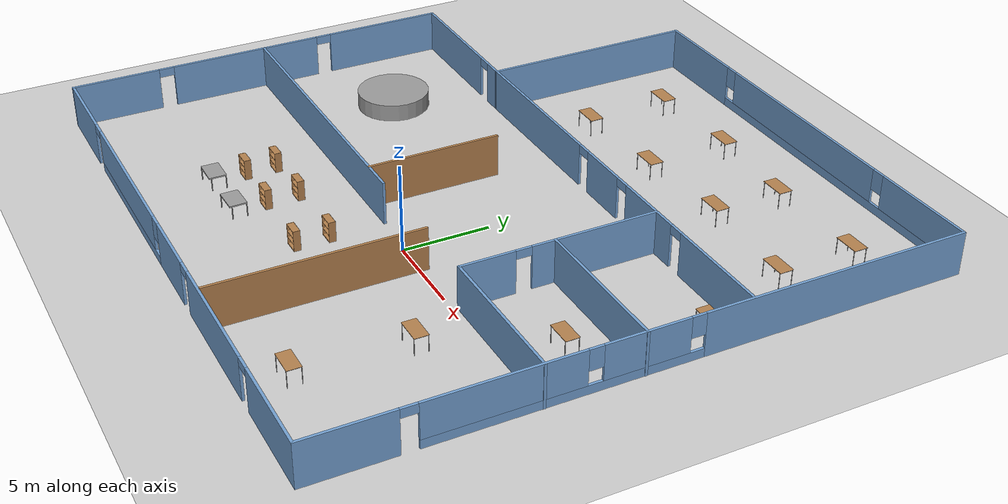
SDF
<sdf version="1.6">
 <world name="default">
  <light name="sun" type="directional">
   <pose>0 0 10 0 -0 0</pose>
   <diffuse>0.8 0.8 0.8 1</diffuse>
   <attenuation>
    <range>1000</range>
    <constant>0.9</constant>
    <linear>0.01</linear>
    <quadratic>0.001</quadratic>
   </attenuation>
   <direction>-0.5 0.1 -0.9</direction>
   <specular>0.1 0.1 0.1 1</specular>
  </light>
  <model name="ground_plane">
   <static>1</static>
   <link name="link">
    <collision name="collision">
     <geometry><plane><normal>0 0 1</normal><size>100 100</size></plane></geometry>
     <surface><friction><ode><mu>100</mu><mu2>50</mu2></ode></friction></surface>
    </collision>
    <visual name="visual">
     <cast_shadows>0</cast_shadows>
     <geometry><plane><normal>0 0 1</normal><size>100 100</size></plane></geometry>
     <material>
      <script><uri>file://media/materials/scripts/gazebo.material</uri><name>Gazebo/Grey</name></script>
     </material>
    </visual>
   </link>
  </model>
  <gravity>0 0 -9.8</gravity>
  <magnetic_field>6e-06 2.3e-05 -4.2e-05</magnetic_field>
  <atmosphere type="adiabatic"/>
  <physics name="default_physics" default="0" type="ode">
   <max_step_size>0.001</max_step_size>
   <real_time_factor>1</real_time_factor>
   <real_time_update_rate>1000</real_time_update_rate>
  </physics>
  <scene><ambient>0.4 0.4 0.4 1</ambient><background>0.7 0.7 0.7 1</background><shadows>1</shadows></scene>
  <audio><device>default</device></audio>
  <spherical_coordinates>
   <surface_model>EARTH_WGS84</surface_model>
   <latitude_deg>0</latitude_deg>
   <longitude_deg>0</longitude_deg>
   <elevation>0</elevation>
   <heading_deg>0</heading_deg>
  </spherical_coordinates>
  <model name="myhouse">
   <pose>-3.19949 6.33 0 0 -0 0</pose>
   <link name="Wall_0">
    <pose>4.61426 17.8 0 0 -0 0</pose>
    <visual name="Wall_0_Visual_0">
     <pose>-10.3159 0 1.25 0 -0 0</pose>
     <geometry><box><size>5.86818 0.15 2.5</size></box></geometry>
     <material>
      <script><uri>file://media/materials/scripts/gazebo.material</uri><name>Gazebo/Grey</name></script>
      <ambient>0.447059 0.623529 0.811765 1</ambient>
     </material>
     <meta><layer>0</layer></meta>
    </visual>
    <collision name="Wall_0_Collision_0">
     <geometry><box><size>5.86818 0.15 2.5</size></box></geometry>
     <pose>-10.3159 0 1.25 0 -0 0</pose>
    </collision>
    <visual name="Wall_0_Visual_1">
     <pose>2.93409 0 0.25 0 -0 0</pose>
     <geometry><box><size>20.6318 0.15 0.5</size></box></geometry>
     <material>
      <script><uri>file://media/materials/scripts/gazebo.material</uri><name>Gazebo/Grey</name></script>
      <ambient>0.447059 0.623529 0.811765 1</ambient>
     </material>
     <meta><layer>0</layer></meta>
    </visual>
    <collision name="Wall_0_Collision_1">
     <geometry><box><size>20.6318 0.15 0.5</size></box></geometry>
     <pose>2.93409 0 0.25 0 -0 0</pose>
    </collision>
    <visual name="Wall_0_Visual_2">
     <pose>-0.192398 0 1.5 0 -0 0</pose>
     <geometry><box><size>12.7788 0.15 2</size></box></geometry>
     <material>
      <script><uri>file://media/materials/scripts/gazebo.material</uri><name>Gazebo/Grey</name></script>
      <ambient>0.447059 0.623529 0.811765 1</ambient>
     </material>
     <meta><layer>0</layer></meta>
    </visual>
    <collision name="Wall_0_Collision_2">
     <geometry><box><size>12.7788 0.15 2</size></box></geometry>
     <pose>-0.192398 0 1.5 0 -0 0</pose>
    </collision>
    <visual name="Wall_0_Visual_3">
     <pose>10.1235 0 1.5 0 -0 0</pose>
     <geometry><box><size>6.25298 0.15 2</size></box></geometry>
     <material>
      <script><uri>file://media/materials/scripts/gazebo.material</uri><name>Gazebo/Grey</name></script>
      <ambient>0.447059 0.623529 0.811765 1</ambient>
     </material>
     <meta><layer>0</layer></meta>
    </visual>
    <collision name="Wall_0_Collision_3">
     <geometry><box><size>6.25298 0.15 2</size></box></geometry>
     <pose>10.1235 0 1.5 0 -0 0</pose>
    </collision>
    <visual name="Wall_0_Visual_4">
     <pose>-6.98182 0 1.9 0 -0 0</pose>
     <geometry><box><size>0.8 0.15 1.2</size></box></geometry>
     <material>
      <script><uri>file://media/materials/scripts/gazebo.material</uri><name>Gazebo/Grey</name></script>
      <ambient>0.447059 0.623529 0.811765 1</ambient>
     </material>
     <meta><layer>0</layer></meta>
    </visual>
    <collision name="Wall_0_Collision_4">
     <geometry><box><size>0.8 0.15 1.2</size></box></geometry>
     <pose>-6.98182 0 1.9 0 -0 0</pose>
    </collision>
    <visual name="Wall_0_Visual_5">
     <pose>6.59703 0 1.9 0 -0 0</pose>
     <geometry><box><size>0.8 0.15 1.2</size></box></geometry>
     <material>
      <script><uri>file://media/materials/scripts/gazebo.material</uri><name>Gazebo/Grey</name></script>
      <ambient>0.447059 0.623529 0.811765 1</ambient>
     </material>
     <meta><layer>0</layer></meta>
    </visual>
    <collision name="Wall_0_Collision_5">
     <geometry><box><size>0.8 0.15 1.2</size></box></geometry>
     <pose>6.59703 0 1.9 0 -0 0</pose>
    </collision>
   </link>
   <link name="Wall_1">
    <pose>17.7893 -0 0 0 -0 -1.5708</pose>
    <visual name="Wall_1_Visual_0">
     <pose>-10.1951 0 1.25 0 -0 0</pose>
     <geometry><box><size>15.3597 0.15 2.5</size></box></geometry>
     <material>
      <script><uri>file://media/materials/scripts/gazebo.material</uri><name>Gazebo/Grey</name></script>
      <ambient>0.447059 0.623529 0.811765 1</ambient>
     </material>
     <meta><layer>0</layer></meta>
    </visual>
    <collision name="Wall_1_Collision_0">
     <geometry><box><size>15.3597 0.15 2.5</size></box></geometry>
     <pose>-10.1951 0 1.25 0 -0 0</pose>
    </collision>
    <visual name="Wall_1_Visual_1">
     <pose>15.4336 0 1.25 0 -0 0</pose>
     <geometry><box><size>4.88286 0.15 2.5</size></box></geometry>
     <material>
      <script><uri>file://media/materials/scripts/gazebo.material</uri><name>Gazebo/Grey</name></script>
      <ambient>0.447059 0.623529 0.811765 1</ambient>
     </material>
     <meta><layer>0</layer></meta>
    </visual>
    <collision name="Wall_1_Collision_1">
     <geometry><box><size>4.88286 0.15 2.5</size></box></geometry>
     <pose>15.4336 0 1.25 0 -0 0</pose>
    </collision>
    <visual name="Wall_1_Visual_2">
     <pose>4.78844 0 0.25 0 -0 0</pose>
     <geometry><box><size>14.6074 0.15 0.5</size></box></geometry>
     <material>
      <script><uri>file://media/materials/scripts/gazebo.material</uri><name>Gazebo/Grey</name></script>
      <ambient>0.447059 0.623529 0.811765 1</ambient>
     </material>
     <meta><layer>0</layer></meta>
    </visual>
    <collision name="Wall_1_Collision_2">
     <geometry><box><size>14.6074 0.15 0.5</size></box></geometry>
     <pose>4.78844 0 0.25 0 -0 0</pose>
    </collision>
    <visual name="Wall_1_Visual_3">
     <pose>0.613666 0 1.5 0 -0 0</pose>
     <geometry><box><size>4.65784 0.15 2</size></box></geometry>
     <material>
      <script><uri>file://media/materials/scripts/gazebo.material</uri><name>Gazebo/Grey</name></script>
      <ambient>0.447059 0.623529 0.811765 1</ambient>
     </material>
     <meta><layer>0</layer></meta>
    </visual>
    <collision name="Wall_1_Collision_3">
     <geometry><box><size>4.65784 0.15 2</size></box></geometry>
     <pose>0.613666 0 1.5 0 -0 0</pose>
    </collision>
    <visual name="Wall_1_Visual_4">
     <pose>7.91736 0 1.5 0 -0 0</pose>
     <geometry><box><size>8.34956 0.15 2</size></box></geometry>
     <material>
      <script><uri>file://media/materials/scripts/gazebo.material</uri><name>Gazebo/Grey</name></script>
      <ambient>0.447059 0.623529 0.811765 1</ambient>
     </material>
     <meta><layer>0</layer></meta>
    </visual>
    <collision name="Wall_1_Collision_4">
     <geometry><box><size>8.34956 0.15 2</size></box></geometry>
     <pose>7.91736 0 1.5 0 -0 0</pose>
    </collision>
    <visual name="Wall_1_Visual_5">
     <pose>-2.11525 0 1.9 0 -0 0</pose>
     <geometry><box><size>0.8 0.15 1.2</size></box></geometry>
     <material>
      <script><uri>file://media/materials/scripts/gazebo.material</uri><name>Gazebo/Grey</name></script>
      <ambient>0.447059 0.623529 0.811765 1</ambient>
     </material>
     <meta><layer>0</layer></meta>
    </visual>
    <collision name="Wall_1_Collision_5">
     <geometry><box><size>0.8 0.15 1.2</size></box></geometry>
     <pose>-2.11525 0 1.9 0 -0 0</pose>
    </collision>
    <visual name="Wall_1_Visual_6">
     <pose>3.34259 0 1.9 0 -0 0</pose>
     <geometry><box><size>0.8 0.15 1.2</size></box></geometry>
     <material>
      <script><uri>file://media/materials/scripts/gazebo.material</uri><name>Gazebo/Grey</name></script>
      <ambient>0.447059 0.623529 0.811765 1</ambient>
     </material>
     <meta><layer>0</layer></meta>
    </visual>
    <collision name="Wall_1_Collision_6">
     <geometry><box><size>0.8 0.15 1.2</size></box></geometry>
     <pose>3.34259 0 1.9 0 -0 0</pose>
    </collision>
    <visual name="Wall_1_Visual_7">
     <pose>12.5421 0 2.25 0 -0 0</pose>
     <geometry><box><size>0.9 0.15 0.5</size></box></geometry>
     <material>
      <script><uri>file://media/materials/scripts/gazebo.material</uri><name>Gazebo/Grey</name></script>
      <ambient>0.447059 0.623529 0.811765 1</ambient>
     </material>
     <meta><layer>0</layer></meta>
    </visual>
    <collision name="Wall_1_Collision_7">
     <geometry><box><size>0.9 0.15 0.5</size></box></geometry>
     <pose>12.5421 0 2.25 0 -0 0</pose>
    </collision>
   </link>
   <link name="Wall_10">
    <pose>9.21154 -0.400105 0 0 -0 -1.5708</pose>
    <visual name="Wall_10_Visual_0">
     <pose>-2.03081 0 1.25 0 -0 0</pose>
     <geometry><box><size>7.26684 0.15 2.5</size></box></geometry>
     <material>
      <script><uri>file://media/materials/scripts/gazebo.material</uri><name>Gazebo/Grey</name></script>
      <ambient>0.447059 0.623529 0.811765 1</ambient>
     </material>
     <meta><layer>0</layer></meta>
    </visual>
    <collision name="Wall_10_Collision_0">
     <geometry><box><size>7.26684 0.15 2.5</size></box></geometry>
     <pose>-2.03081 0 1.25 0 -0 0</pose>
    </collision>
    <visual name="Wall_10_Visual_1">
     <pose>4.08342 0 1.25 0 -0 0</pose>
     <geometry><box><size>3.16161 0.15 2.5</size></box></geometry>
     <material>
      <script><uri>file://media/materials/scripts/gazebo.material</uri><name>Gazebo/Grey</name></script>
      <ambient>0.447059 0.623529 0.811765 1</ambient>
     </material>
     <meta><layer>0</layer></meta>
    </visual>
    <collision name="Wall_10_Collision_1">
     <geometry><box><size>3.16161 0.15 2.5</size></box></geometry>
     <pose>4.08342 0 1.25 0 -0 0</pose>
    </collision>
    <visual name="Wall_10_Visual_2">
     <pose>2.05262 0 2.25 0 -0 0</pose>
     <geometry><box><size>0.9 0.15 0.5</size></box></geometry>
     <material>
      <script><uri>file://media/materials/scripts/gazebo.material</uri><name>Gazebo/Grey</name></script>
      <ambient>0.447059 0.623529 0.811765 1</ambient>
     </material>
     <meta><layer>0</layer></meta>
    </visual>
    <collision name="Wall_10_Collision_2">
     <geometry><box><size>0.9 0.15 0.5</size></box></geometry>
     <pose>2.05262 0 2.25 0 -0 0</pose>
    </collision>
   </link>
   <link name="Wall_13">
    <collision name="Wall_13_Collision">
     <geometry><box><size>8.75 0.15 2.5</size></box></geometry>
     <pose>0 0 1.25 0 -0 0</pose>
    </collision>
    <visual name="Wall_13_Visual">
     <pose>0 0 1.25 0 -0 0</pose>
     <geometry><box><size>8.75 0.15 2.5</size></box></geometry>
     <material>
      <script><uri>file://media/materials/scripts/gazebo.material</uri><name>Gazebo/Grey</name></script>
      <ambient>0.447059 0.623529 0.811765 1</ambient>
     </material>
     <meta><layer>0</layer></meta>
    </visual>
    <pose>13.5115 -5.98933 0 0 -0 0</pose>
   </link>
   <link name="Wall_15">
    <collision name="Wall_15_Collision">
     <geometry><box><size>8.75 0.15 2.5</size></box></geometry>
     <pose>0 0 1.25 0 -0 0</pose>
    </collision>
    <visual name="Wall_15_Visual">
     <pose>0 0 1.25 0 -0 0</pose>
     <geometry><box><size>8.75 0.15 2.5</size></box></geometry>
     <material>
      <script><uri>file://media/materials/scripts/gazebo.material</uri><name>Gazebo/Grey</name></script>
      <ambient>0.447059 0.623529 0.811765 1</ambient>
     </material>
     <meta><layer>0</layer></meta>
    </visual>
    <pose>13.5114 -0.669808 0 0 -0 0</pose>
   </link>
   <link name="Wall_17">
    <collision name="Wall_17_Collision">
     <geometry><box><size>18.25 0.15 2.5</size></box></geometry>
     <pose>0 0 1.25 0 -0 0</pose>
    </collision>
    <visual name="Wall_17_Visual">
     <pose>0 0 1.25 0 -0 0</pose>
     <geometry><box><size>18.25 0.15 2.5</size></box></geometry>
     <material>
      <script><uri>file://media/materials/scripts/gazebo.material</uri><name>Gazebo/Grey</name></script>
      <ambient>0.447059 0.623529 0.811765 1</ambient>
     </material>
     <meta><layer>0</layer></meta>
    </visual>
    <pose>-8.72356 -6.06182 0 0 -0 0</pose>
   </link>
   <link name="Wall_19">
    <collision name="Wall_19_Collision">
     <geometry><box><size>7.75 0.15 2.5</size></box></geometry>
     <pose>0 0 1.25 0 -0 0</pose>
    </collision>
    <visual name="Wall_19_Visual">
     <pose>0 0 1.25 0 -0 0</pose>
     <geometry><box><size>7.75 0.15 2.5</size></box></geometry>
     <material>
      <script><uri>file://media/materials/scripts/gazebo.material</uri><name>Gazebo/Wood</name></script>
      <ambient>1 1 1 1</ambient>
     </material>
     <meta><layer>0</layer></meta>
    </visual>
    <pose>-1.57819 -2.2167 0 0 -0 1.5708</pose>
   </link>
   <link name="Wall_2">
    <pose>-0.010735 -17.8 0 0 -0 3.14159</pose>
    <visual name="Wall_2_Visual_0">
     <pose>-15.0259 0 1.25 0 -0 0</pose>
     <geometry><box><size>5.69813 0.15 2.5</size></box></geometry>
     <material>
      <script><uri>file://media/materials/scripts/gazebo.material</uri><name>Gazebo/Grey</name></script>
      <ambient>0.447059 0.623529 0.811765 1</ambient>
     </material>
     <meta><layer>0</layer></meta>
    </visual>
    <collision name="Wall_2_Collision_0">
     <geometry><box><size>5.69813 0.15 2.5</size></box></geometry>
     <pose>-15.0259 0 1.25 0 -0 0</pose>
    </collision>
    <visual name="Wall_2_Visual_1">
     <pose>-7.50561 0 1.25 0 -0 0</pose>
     <geometry><box><size>7.54251 0.15 2.5</size></box></geometry>
     <material>
      <script><uri>file://media/materials/scripts/gazebo.material</uri><name>Gazebo/Grey</name></script>
      <ambient>0.447059 0.623529 0.811765 1</ambient>
     </material>
     <meta><layer>0</layer></meta>
    </visual>
    <collision name="Wall_2_Collision_1">
     <geometry><box><size>7.54251 0.15 2.5</size></box></geometry>
     <pose>-7.50561 0 1.25 0 -0 0</pose>
    </collision>
    <visual name="Wall_2_Visual_2">
     <pose>-0.885398 0 1.25 0 -0 0</pose>
     <geometry><box><size>3.89792 0.15 2.5</size></box></geometry>
     <material>
      <script><uri>file://media/materials/scripts/gazebo.material</uri><name>Gazebo/Grey</name></script>
      <ambient>0.447059 0.623529 0.811765 1</ambient>
     </material>
     <meta><layer>0</layer></meta>
    </visual>
    <collision name="Wall_2_Collision_2">
     <geometry><box><size>3.89792 0.15 2.5</size></box></geometry>
     <pose>-0.885398 0 1.25 0 -0 0</pose>
    </collision>
    <visual name="Wall_2_Visual_3">
     <pose>15.3234 0 1.25 0 -0 0</pose>
     <geometry><box><size>5.10327 0.15 2.5</size></box></geometry>
     <material>
      <script><uri>file://media/materials/scripts/gazebo.material</uri><name>Gazebo/Grey</name></script>
      <ambient>0.447059 0.623529 0.811765 1</ambient>
     </material>
     <meta><layer>0</layer></meta>
    </visual>
    <collision name="Wall_2_Collision_3">
     <geometry><box><size>5.10327 0.15 2.5</size></box></geometry>
     <pose>15.3234 0 1.25 0 -0 0</pose>
    </collision>
    <visual name="Wall_2_Visual_4">
     <pose>6.46765 0 0.25 0 -0 0</pose>
     <geometry><box><size>10.8082 0.15 0.5</size></box></geometry>
     <material>
      <script><uri>file://media/materials/scripts/gazebo.material</uri><name>Gazebo/Grey</name></script>
      <ambient>0.447059 0.623529 0.811765 1</ambient>
     </material>
     <meta><layer>0</layer></meta>
    </visual>
    <collision name="Wall_2_Collision_4">
     <geometry><box><size>10.8082 0.15 0.5</size></box></geometry>
     <pose>6.46765 0 0.25 0 -0 0</pose>
    </collision>
    <visual name="Wall_2_Visual_5">
     <pose>6.86765 0 1.5 0 -0 0</pose>
     <geometry><box><size>10.0082 0.15 2</size></box></geometry>
     <material>
      <script><uri>file://media/materials/scripts/gazebo.material</uri><name>Gazebo/Grey</name></script>
      <ambient>0.447059 0.623529 0.811765 1</ambient>
     </material>
     <meta><layer>0</layer></meta>
    </visual>
    <collision name="Wall_2_Collision_5">
     <geometry><box><size>10.0082 0.15 2</size></box></geometry>
     <pose>6.86765 0 1.5 0 -0 0</pose>
    </collision>
    <visual name="Wall_2_Visual_6">
     <pose>1.46356 0 1.9 0 -0 0</pose>
     <geometry><box><size>0.8 0.15 1.2</size></box></geometry>
     <material>
      <script><uri>file://media/materials/scripts/gazebo.material</uri><name>Gazebo/Grey</name></script>
      <ambient>0.447059 0.623529 0.811765 1</ambient>
     </material>
     <meta><layer>0</layer></meta>
    </visual>
    <collision name="Wall_2_Collision_6">
     <geometry><box><size>0.8 0.15 1.2</size></box></geometry>
     <pose>1.46356 0 1.9 0 -0 0</pose>
    </collision>
    <visual name="Wall_2_Visual_7">
     <pose>-11.7269 0 2.25 0 -0 0</pose>
     <geometry><box><size>0.9 0.15 0.5</size></box></geometry>
     <material>
      <script><uri>file://media/materials/scripts/gazebo.material</uri><name>Gazebo/Grey</name></script>
      <ambient>0.447059 0.623529 0.811765 1</ambient>
     </material>
     <meta><layer>0</layer></meta>
    </visual>
    <collision name="Wall_2_Collision_7">
     <geometry><box><size>0.9 0.15 0.5</size></box></geometry>
     <pose>-11.7269 0 2.25 0 -0 0</pose>
    </collision>
    <visual name="Wall_2_Visual_8">
     <pose>-3.28436 0 2.25 0 -0 0</pose>
     <geometry><box><size>0.9 0.15 0.5</size></box></geometry>
     <material>
      <script><uri>file://media/materials/scripts/gazebo.material</uri><name>Gazebo/Grey</name></script>
      <ambient>0.447059 0.623529 0.811765 1</ambient>
     </material>
     <meta><layer>0</layer></meta>
    </visual>
    <collision name="Wall_2_Collision_8">
     <geometry><box><size>0.9 0.15 0.5</size></box></geometry>
     <pose>-3.28436 0 2.25 0 -0 0</pose>
    </collision>
    <visual name="Wall_2_Visual_9">
     <pose>12.3217 0 2.25 0 -0 0</pose>
     <geometry><box><size>0.9 0.15 0.5</size></box></geometry>
     <material>
      <script><uri>file://media/materials/scripts/gazebo.material</uri><name>Gazebo/Grey</name></script>
      <ambient>0.447059 0.623529 0.811765 1</ambient>
     </material>
     <meta><layer>0</layer></meta>
    </visual>
    <collision name="Wall_2_Collision_9">
     <geometry><box><size>0.9 0.15 0.5</size></box></geometry>
     <pose>12.3217 0 2.25 0 -0 0</pose>
    </collision>
   </link>
   <link name="Wall_23">
    <collision name="Wall_23_Collision">
     <geometry><box><size>12 0.15 2.5</size></box></geometry>
     <pose>0 0 1.25 0 -0 0</pose>
    </collision>
    <visual name="Wall_23_Visual">
     <pose>0 0 1.25 0 -0 0</pose>
     <geometry><box><size>12 0.15 2.5</size></box></geometry>
     <material>
      <script><uri>file://media/materials/scripts/gazebo.material</uri><name>Gazebo/Wood</name></script>
      <ambient>1 1 1 1</ambient>
     </material>
     <meta><layer>0</layer></meta>
    </visual>
    <pose>5.32796 -11.8207 0 0 -0 1.5708</pose>
   </link>
   <link name="Wall_3">
    <pose>-17.8107 -6.25 0 0 -0 1.5708</pose>
    <visual name="Wall_3_Visual_0">
     <pose>-9.02802 0 1.25 0 -0 0</pose>
     <geometry><box><size>5.19397 0.15 2.5</size></box></geometry>
     <material>
      <script><uri>file://media/materials/scripts/gazebo.material</uri><name>Gazebo/Grey</name></script>
      <ambient>0.447059 0.623529 0.811765 1</ambient>
     </material>
     <meta><layer>0</layer></meta>
    </visual>
    <collision name="Wall_3_Collision_0">
     <geometry><box><size>5.19397 0.15 2.5</size></box></geometry>
     <pose>-9.02802 0 1.25 0 -0 0</pose>
    </collision>
    <visual name="Wall_3_Visual_1">
     <pose>-0.961315 0 1.25 0 -0 0</pose>
     <geometry><box><size>9.13944 0.15 2.5</size></box></geometry>
     <material>
      <script><uri>file://media/materials/scripts/gazebo.material</uri><name>Gazebo/Grey</name></script>
      <ambient>0.447059 0.623529 0.811765 1</ambient>
     </material>
     <meta><layer>0</layer></meta>
    </visual>
    <collision name="Wall_3_Collision_1">
     <geometry><box><size>9.13944 0.15 2.5</size></box></geometry>
     <pose>-0.961315 0 1.25 0 -0 0</pose>
    </collision>
    <visual name="Wall_3_Visual_2">
     <pose>8.0667 0 1.25 0 -0 0</pose>
     <geometry><box><size>7.1166 0.15 2.5</size></box></geometry>
     <material>
      <script><uri>file://media/materials/scripts/gazebo.material</uri><name>Gazebo/Grey</name></script>
      <ambient>0.447059 0.623529 0.811765 1</ambient>
     </material>
     <meta><layer>0</layer></meta>
    </visual>
    <collision name="Wall_3_Collision_2">
     <geometry><box><size>7.1166 0.15 2.5</size></box></geometry>
     <pose>8.0667 0 1.25 0 -0 0</pose>
    </collision>
    <visual name="Wall_3_Visual_3">
     <pose>-5.98103 0 2.25 0 -0 0</pose>
     <geometry><box><size>0.9 0.15 0.5</size></box></geometry>
     <material>
      <script><uri>file://media/materials/scripts/gazebo.material</uri><name>Gazebo/Grey</name></script>
      <ambient>0.447059 0.623529 0.811765 1</ambient>
     </material>
     <meta><layer>0</layer></meta>
    </visual>
    <collision name="Wall_3_Collision_3">
     <geometry><box><size>0.9 0.15 0.5</size></box></geometry>
     <pose>-5.98103 0 2.25 0 -0 0</pose>
    </collision>
    <visual name="Wall_3_Visual_4">
     <pose>4.0584 0 2.25 0 -0 0</pose>
     <geometry><box><size>0.9 0.15 0.5</size></box></geometry>
     <material>
      <script><uri>file://media/materials/scripts/gazebo.material</uri><name>Gazebo/Grey</name></script>
      <ambient>0.447059 0.623529 0.811765 1</ambient>
     </material>
     <meta><layer>0</layer></meta>
    </visual>
    <collision name="Wall_3_Collision_4">
     <geometry><box><size>0.9 0.15 0.5</size></box></geometry>
     <pose>4.0584 0 2.25 0 -0 0</pose>
    </collision>
   </link>
   <link name="Wall_5">
    <collision name="Wall_5_Collision">
     <geometry><box><size>12.75 0.15 2.5</size></box></geometry>
     <pose>0 0 1.25 0 -0 0</pose>
    </collision>
    <visual name="Wall_5_Visual">
     <pose>0 0 1.25 0 -0 0</pose>
     <geometry><box><size>12.75 0.15 2.5</size></box></geometry>
     <material>
      <script><uri>file://media/materials/scripts/gazebo.material</uri><name>Gazebo/Grey</name></script>
      <ambient>0.447059 0.623529 0.811765 1</ambient>
     </material>
     <meta><layer>0</layer></meta>
    </visual>
    <pose>-8.56073 11.5 0 0 -0 -1.5708</pose>
   </link>
   <link name="Wall_6">
    <pose>-13.1857 5.25 0 0 -0 3.13078</pose>
    <visual name="Wall_6_Visual_0">
     <pose>-4.09582 0 1.25 0 -0 0</pose>
     <geometry><box><size>1.2089 0.15 2.5</size></box></geometry>
     <material>
      <script><uri>file://media/materials/scripts/gazebo.material</uri><name>Gazebo/Grey</name></script>
      <ambient>0.447059 0.623529 0.811765 1</ambient>
     </material>
     <meta><layer>0</layer></meta>
    </visual>
    <collision name="Wall_6_Collision_0">
     <geometry><box><size>1.2089 0.15 2.5</size></box></geometry>
     <pose>-4.09582 0 1.25 0 -0 0</pose>
    </collision>
    <visual name="Wall_6_Visual_1">
     <pose>1.05445 0 1.25 0 -0 0</pose>
     <geometry><box><size>7.29164 0.15 2.5</size></box></geometry>
     <material>
      <script><uri>file://media/materials/scripts/gazebo.material</uri><name>Gazebo/Grey</name></script>
      <ambient>0.447059 0.623529 0.811765 1</ambient>
     </material>
     <meta><layer>0</layer></meta>
    </visual>
    <collision name="Wall_6_Collision_1">
     <geometry><box><size>7.29164 0.15 2.5</size></box></geometry>
     <pose>1.05445 0 1.25 0 -0 0</pose>
    </collision>
    <visual name="Wall_6_Visual_2">
     <pose>-3.04137 0 2.25 0 -0 0</pose>
     <geometry><box><size>0.9 0.15 0.5</size></box></geometry>
     <material>
      <script><uri>file://media/materials/scripts/gazebo.material</uri><name>Gazebo/Grey</name></script>
      <ambient>0.447059 0.623529 0.811765 1</ambient>
     </material>
     <meta><layer>0</layer></meta>
    </visual>
    <collision name="Wall_6_Collision_2">
     <geometry><box><size>0.9 0.15 0.5</size></box></geometry>
     <pose>-3.04137 0 2.25 0 -0 0</pose>
    </collision>
   </link>
   <link name="Wall_8">
    <pose>4.61426 5.2 0 0 -0 0</pose>
    <visual name="Wall_8_Visual_0">
     <pose>-8.20743 0 1.25 0 -0 0</pose>
     <geometry><box><size>10.0851 0.15 2.5</size></box></geometry>
     <material>
      <script><uri>file://media/materials/scripts/gazebo.material</uri><name>Gazebo/Grey</name></script>
      <ambient>0.447059 0.623529 0.811765 1</ambient>
     </material>
     <meta><layer>0</layer></meta>
    </visual>
    <collision name="Wall_8_Collision_0">
     <geometry><box><size>10.0851 0.15 2.5</size></box></geometry>
     <pose>-8.20743 0 1.25 0 -0 0</pose>
    </collision>
    <visual name="Wall_8_Visual_1">
     <pose>-0.725872 0 1.25 0 -0 0</pose>
     <geometry><box><size>3.07799 0.15 2.5</size></box></geometry>
     <material>
      <script><uri>file://media/materials/scripts/gazebo.material</uri><name>Gazebo/Grey</name></script>
      <ambient>0.447059 0.623529 0.811765 1</ambient>
     </material>
     <meta><layer>0</layer></meta>
    </visual>
    <collision name="Wall_8_Collision_1">
     <geometry><box><size>3.07799 0.15 2.5</size></box></geometry>
     <pose>-0.725872 0 1.25 0 -0 0</pose>
    </collision>
    <visual name="Wall_8_Visual_2">
     <pose>3.86689 0 1.25 0 -0 0</pose>
     <geometry><box><size>4.30753 0.15 2.5</size></box></geometry>
     <material>
      <script><uri>file://media/materials/scripts/gazebo.material</uri><name>Gazebo/Grey</name></script>
      <ambient>0.447059 0.623529 0.811765 1</ambient>
     </material>
     <meta><layer>0</layer></meta>
    </visual>
    <collision name="Wall_8_Collision_2">
     <geometry><box><size>4.30753 0.15 2.5</size></box></geometry>
     <pose>3.86689 0 1.25 0 -0 0</pose>
    </collision>
    <visual name="Wall_8_Visual_3">
     <pose>10.0853 0 1.25 0 -0 0</pose>
     <geometry><box><size>6.32935 0.15 2.5</size></box></geometry>
     <material>
      <script><uri>file://media/materials/scripts/gazebo.material</uri><name>Gazebo/Grey</name></script>
      <ambient>0.447059 0.623529 0.811765 1</ambient>
     </material>
     <meta><layer>0</layer></meta>
    </visual>
    <collision name="Wall_8_Collision_3">
     <geometry><box><size>6.32935 0.15 2.5</size></box></geometry>
     <pose>10.0853 0 1.25 0 -0 0</pose>
    </collision>
    <visual name="Wall_8_Visual_4">
     <pose>-2.71487 0 2.25 0 -0 0</pose>
     <geometry><box><size>0.9 0.15 0.5</size></box></geometry>
     <material>
      <script><uri>file://media/materials/scripts/gazebo.material</uri><name>Gazebo/Grey</name></script>
      <ambient>0.447059 0.623529 0.811765 1</ambient>
     </material>
     <meta><layer>0</layer></meta>
    </visual>
    <collision name="Wall_8_Collision_4">
     <geometry><box><size>0.9 0.15 0.5</size></box></geometry>
     <pose>-2.71487 0 2.25 0 -0 0</pose>
    </collision>
    <visual name="Wall_8_Visual_5">
     <pose>1.26312 0 2.25 0 -0 0</pose>
     <geometry><box><size>0.9 0.15 0.5</size></box></geometry>
     <material>
      <script><uri>file://media/materials/scripts/gazebo.material</uri><name>Gazebo/Grey</name></script>
      <ambient>0.447059 0.623529 0.811765 1</ambient>
     </material>
     <meta><layer>0</layer></meta>
    </visual>
    <collision name="Wall_8_Collision_5">
     <geometry><box><size>0.9 0.15 0.5</size></box></geometry>
     <pose>1.26312 0 2.25 0 -0 0</pose>
    </collision>
    <visual name="Wall_8_Visual_6">
     <pose>6.47065 0 2.25 0 -0 0</pose>
     <geometry><box><size>0.9 0.15 0.5</size></box></geometry>
     <material>
      <script><uri>file://media/materials/scripts/gazebo.material</uri><name>Gazebo/Grey</name></script>
      <ambient>0.447059 0.623529 0.811765 1</ambient>
     </material>
     <meta><layer>0</layer></meta>
    </visual>
    <collision name="Wall_8_Collision_6">
     <geometry><box><size>0.9 0.15 0.5</size></box></geometry>
     <pose>6.47065 0 2.25 0 -0 0</pose>
    </collision>
   </link>
   <static>1</static>
  </model>
  <model name="mydesk">
   <link name="link_0">
    <inertial>
     <mass>1</mass>
     <inertia>
      <ixx>0.166667</ixx>
      <ixy>0</ixy>
      <ixz>0</ixz>
      <iyy>0.166667</iyy>
      <iyz>0</iyz>
      <izz>0.166667</izz>
     </inertia>
    </inertial>
    <pose>0 0.022 0.32 0 -0 0</pose>
    <visual name="visual">
     <geometry><box><size>1.5 1 0.08</size></box></geometry>
     <material>
      <lighting>1</lighting>
      <script><uri>file://media/materials/scripts/gazebo.material</uri><name>Gazebo/Grey</name></script>
      <shader type="vertex"><normal_map>__default__</normal_map></shader>
      <ambient>0.3 0.3 0.3 1</ambient>
      <diffuse>0.7 0.7 0.7 1</diffuse>
      <specular>0.01 0.01 0.01 1</specular>
      <emissive>0 0 0 1</emissive>
     </material>
    </visual>
    <collision name="collision">
     <geometry><box><size>1.5 1 0.08</size></box></geometry>
     <surface>
      <friction>
       <ode><mu>1</mu><mu2>1</mu2><fdir1>0 0 0</fdir1><slip1>0</slip1><slip2>0</slip2></ode>
       <torsional>
        <coefficient>1</coefficient>
        <patch_radius>0</patch_radius>
        <surface_radius>0</surface_radius>
        <use_patch_radius>1</use_patch_radius>
        <ode><slip>0</slip></ode>
       </torsional>
      </friction>
      <bounce><restitution_coefficient>0</restitution_coefficient><threshold>1e+06</threshold></bounce>
      <contact>
       <collide_without_contact>0</collide_without_contact>
       <collide_without_contact_bitmask>1</collide_without_contact_bitmask>
       <collide_bitmask>1</collide_bitmask>
       <ode>
        <soft_cfm>0</soft_cfm>
        <soft_erp>0.2</soft_erp>
        <kp>1e+13</kp>
        <kd>1</kd>
        <max_vel>0.01</max_vel>
        <min_depth>0</min_depth>
       </ode>
       <bullet>
        <split_impulse>1</split_impulse>
        <split_impulse_penetration_threshold>-0.01</split_impulse_penetration_threshold>
        <soft_cfm>0</soft_cfm>
        <soft_erp>0.2</soft_erp>
        <kp>1e+13</kp>
        <kd>1</kd>
       </bullet>
      </contact>
     </surface>
    </collision>
   </link>
   <link name="link_1">
    <inertial>
     <mass>1</mass>
     <inertia><ixx>0.145833</ixx><ixy>0</ixy><ixz>0</ixz><iyy>0.145833</iyy><iyz>0</iyz><izz>0.125</izz></inertia>
     <pose>0 0 -0.02 0 -0 0</pose>
    </inertial>
    <pose>-0.72 0.382 -0.08 0 -0 0</pose>
    <visual name="visual">
     <geometry><cylinder><radius>0.03</radius><length>0.8</length></cylinder></geometry>
     <material>
      <lighting>1</lighting>
      <script><uri>file://media/materials/scripts/gazebo.material</uri><name>Gazebo/Grey</name></script>
      <shader type="vertex"><normal_map>__default__</normal_map></shader>
      <ambient>0.3 0.3 0.3 1</ambient>
      <diffuse>0.7 0.7 0.7 1</diffuse>
      <specular>0.01 0.01 0.01 1</specular>
      <emissive>0 0 0 1</emissive>
     </material>
    </visual>
    <collision name="collision">
     <geometry><cylinder><radius>0.03</radius><length>0.8</length></cylinder></geometry>
     <surface>
      <friction>
       <ode><mu>1</mu><mu2>1</mu2><fdir1>0 0 0</fdir1><slip1>0</slip1><slip2>0</slip2></ode>
       <torsional>
        <coefficient>1</coefficient>
        <patch_radius>0</patch_radius>
        <surface_radius>0</surface_radius>
        <use_patch_radius>1</use_patch_radius>
        <ode><slip>0</slip></ode>
       </torsional>
      </friction>
      <bounce><restitution_coefficient>0</restitution_coefficient><threshold>1e+06</threshold></bounce>
      <contact>
       <collide_without_contact>0</collide_without_contact>
       <collide_without_contact_bitmask>1</collide_without_contact_bitmask>
       <collide_bitmask>1</collide_bitmask>
       <ode>
        <soft_cfm>0</soft_cfm>
        <soft_erp>0.2</soft_erp>
        <kp>1e+13</kp>
        <kd>1</kd>
        <max_vel>0.01</max_vel>
        <min_depth>0</min_depth>
       </ode>
       <bullet>
        <split_impulse>1</split_impulse>
        <split_impulse_penetration_threshold>-0.01</split_impulse_penetration_threshold>
        <soft_cfm>0</soft_cfm>
        <soft_erp>0.2</soft_erp>
        <kp>1e+13</kp>
        <kd>1</kd>
       </bullet>
      </contact>
     </surface>
    </collision>
   </link>
   <link name="link_1_clone">
    <inertial>
     <mass>1</mass>
     <inertia><ixx>0.145833</ixx><ixy>0</ixy><ixz>0</ixz><iyy>0.145833</iyy><iyz>0</iyz><izz>0.125</izz></inertia>
     <pose>0 0 -0.02 0 -0 0</pose>
    </inertial>
    <pose>-0.72 -0.448 -0.08 0 -0 0</pose>
    <visual name="visual">
     <geometry><cylinder><radius>0.03</radius><length>0.8</length></cylinder></geometry>
     <material>
      <lighting>1</lighting>
      <script><uri>file://media/materials/scripts/gazebo.material</uri><name>Gazebo/Grey</name></script>
      <shader type="vertex"><normal_map>__default__</normal_map></shader>
      <ambient>0.3 0.3 0.3 1</ambient>
      <diffuse>0.7 0.7 0.7 1</diffuse>
      <specular>0.01 0.01 0.01 1</specular>
      <emissive>0 0 0 1</emissive>
     </material>
    </visual>
    <collision name="collision">
     <geometry><cylinder><radius>0.03</radius><length>0.8</length></cylinder></geometry>
     <surface>
      <friction>
       <ode><mu>1</mu><mu2>1</mu2><fdir1>0 0 0</fdir1><slip1>0</slip1><slip2>0</slip2></ode>
       <torsional>
        <coefficient>1</coefficient>
        <patch_radius>0</patch_radius>
        <surface_radius>0</surface_radius>
        <use_patch_radius>1</use_patch_radius>
        <ode><slip>0</slip></ode>
       </torsional>
      </friction>
      <bounce><restitution_coefficient>0</restitution_coefficient><threshold>1e+06</threshold></bounce>
      <contact>
       <collide_without_contact>0</collide_without_contact>
       <collide_without_contact_bitmask>1</collide_without_contact_bitmask>
       <collide_bitmask>1</collide_bitmask>
       <ode>
        <soft_cfm>0</soft_cfm>
        <soft_erp>0.2</soft_erp>
        <kp>1e+13</kp>
        <kd>1</kd>
        <max_vel>0.01</max_vel>
        <min_depth>0</min_depth>
       </ode>
       <bullet>
        <split_impulse>1</split_impulse>
        <split_impulse_penetration_threshold>-0.01</split_impulse_penetration_threshold>
        <soft_cfm>0</soft_cfm>
        <soft_erp>0.2</soft_erp>
        <kp>1e+13</kp>
        <kd>1</kd>
       </bullet>
      </contact>
     </surface>
    </collision>
   </link>
   <link name="link_1_clone_0">
    <inertial>
     <mass>1</mass>
     <inertia><ixx>0.145833</ixx><ixy>0</ixy><ixz>0</ixz><iyy>0.145833</iyy><iyz>0</iyz><izz>0.125</izz></inertia>
     <pose>0 0 -0.02 0 -0 0</pose>
    </inertial>
    <pose>0.72 -0.448 -0.08 0 -0 0</pose>
    <visual name="visual">
     <geometry><cylinder><radius>0.03</radius><length>0.8</length></cylinder></geometry>
     <material>
      <lighting>1</lighting>
      <script><uri>file://media/materials/scripts/gazebo.material</uri><name>Gazebo/Grey</name></script>
      <shader type="vertex"><normal_map>__default__</normal_map></shader>
      <ambient>0.3 0.3 0.3 1</ambient>
      <diffuse>0.7 0.7 0.7 1</diffuse>
      <specular>0.01 0.01 0.01 1</specular>
      <emissive>0 0 0 1</emissive>
     </material>
    </visual>
    <collision name="collision">
     <geometry><cylinder><radius>0.03</radius><length>0.8</length></cylinder></geometry>
     <surface>
      <friction>
       <ode><mu>1</mu><mu2>1</mu2><fdir1>0 0 0</fdir1><slip1>0</slip1><slip2>0</slip2></ode>
       <torsional>
        <coefficient>1</coefficient>
        <patch_radius>0</patch_radius>
        <surface_radius>0</surface_radius>
        <use_patch_radius>1</use_patch_radius>
        <ode><slip>0</slip></ode>
       </torsional>
      </friction>
      <bounce><restitution_coefficient>0</restitution_coefficient><threshold>1e+06</threshold></bounce>
      <contact>
       <collide_without_contact>0</collide_without_contact>
       <collide_without_contact_bitmask>1</collide_without_contact_bitmask>
       <collide_bitmask>1</collide_bitmask>
       <ode>
        <soft_cfm>0</soft_cfm>
        <soft_erp>0.2</soft_erp>
        <kp>1e+13</kp>
        <kd>1</kd>
        <max_vel>0.01</max_vel>
        <min_depth>0</min_depth>
       </ode>
       <bullet>
        <split_impulse>1</split_impulse>
        <split_impulse_penetration_threshold>-0.01</split_impulse_penetration_threshold>
        <soft_cfm>0</soft_cfm>
        <soft_erp>0.2</soft_erp>
        <kp>1e+13</kp>
        <kd>1</kd>
       </bullet>
      </contact>
     </surface>
    </collision>
   </link>
   <link name="link_1_clone_1">
    <inertial>
     <mass>1</mass>
     <inertia><ixx>0.145833</ixx><ixy>0</ixy><ixz>0</ixz><iyy>0.145833</iyy><iyz>0</iyz><izz>0.125</izz></inertia>
     <pose>0 0 -0.02 0 -0 0</pose>
    </inertial>
    <pose>0.72 0.492 -0.08 0 -0 0</pose>
    <visual name="visual">
     <geometry><cylinder><radius>0.03</radius><length>0.8</length></cylinder></geometry>
     <material>
      <lighting>1</lighting>
      <script><uri>file://media/materials/scripts/gazebo.material</uri><name>Gazebo/Grey</name></script>
      <shader type="vertex"><normal_map>__default__</normal_map></shader>
      <ambient>0.3 0.3 0.3 1</ambient>
      <diffuse>0.7 0.7 0.7 1</diffuse>
      <specular>0.01 0.01 0.01 1</specular>
      <emissive>0 0 0 1</emissive>
     </material>
    </visual>
    <collision name="collision">
     <geometry><cylinder><radius>0.03</radius><length>0.8</length></cylinder></geometry>
     <surface>
      <friction>
       <ode><mu>1</mu><mu2>1</mu2><fdir1>0 0 0</fdir1><slip1>0</slip1><slip2>0</slip2></ode>
       <torsional>
        <coefficient>1</coefficient>
        <patch_radius>0</patch_radius>
        <surface_radius>0</surface_radius>
        <use_patch_radius>1</use_patch_radius>
        <ode><slip>0</slip></ode>
       </torsional>
      </friction>
      <bounce><restitution_coefficient>0</restitution_coefficient><threshold>1e+06</threshold></bounce>
      <contact>
       <collide_without_contact>0</collide_without_contact>
       <collide_without_contact_bitmask>1</collide_without_contact_bitmask>
       <collide_bitmask>1</collide_bitmask>
       <ode>
        <soft_cfm>0</soft_cfm>
        <soft_erp>0.2</soft_erp>
        <kp>1e+13</kp>
        <kd>1</kd>
        <max_vel>0.01</max_vel>
        <min_depth>0</min_depth>
       </ode>
       <bullet>
        <split_impulse>1</split_impulse>
        <split_impulse_penetration_threshold>-0.01</split_impulse_penetration_threshold>
        <soft_cfm>0</soft_cfm>
        <soft_erp>0.2</soft_erp>
        <kp>1e+13</kp>
        <kd>1</kd>
       </bullet>
      </contact>
     </surface>
    </collision>
   </link>
   <joint name="link_0_JOINT_0" type="fixed">
    <parent>link_0</parent>
    <child>link_1_clone</child>
    <physics>
     <ode><limit><cfm>0</cfm><erp>0.2</erp></limit><suspension><cfm>0</cfm><erp>0.2</erp></suspension></ode>
    </physics>
   </joint>
   <joint name="link_0_JOINT_1" type="fixed">
    <parent>link_0</parent>
    <child>link_1_clone_1</child>
    <physics>
     <ode><limit><cfm>0</cfm><erp>0.2</erp></limit><suspension><cfm>0</cfm><erp>0.2</erp></suspension></ode>
    </physics>
   </joint>
   <joint name="link_0_JOINT_2" type="fixed">
    <parent>link_0</parent>
    <child>link_1_clone_0</child>
    <physics>
     <ode><limit><cfm>0</cfm><erp>0.2</erp></limit><suspension><cfm>0</cfm><erp>0.2</erp></suspension></ode>
    </physics>
   </joint>
   <joint name="link_0_JOINT_3" type="fixed">
    <parent>link_0</parent>
    <child>link_1</child>
    <physics>
     <ode><limit><cfm>0</cfm><erp>0.2</erp></limit><suspension><cfm>0</cfm><erp>0.2</erp></suspension></ode>
    </physics>
   </joint>
   <static>0</static>
   <pose>-7.60063 -6.44078 0.479998 3e-06 3e-06 -3.12126</pose>
  </model>
  <model name="mydesk_clone">
   <link name="link_0">
    <inertial>
     <mass>1</mass>
     <inertia>
      <ixx>0.166667</ixx>
      <ixy>0</ixy>
      <ixz>0</ixz>
      <iyy>0.166667</iyy>
      <iyz>0</iyz>
      <izz>0.166667</izz>
     </inertia>
    </inertial>
    <pose>0 0.022 0.32 0 -0 0</pose>
    <visual name="visual">
     <geometry><box><size>1.5 1 0.08</size></box></geometry>
     <material>
      <lighting>1</lighting>
      <script><uri>file://media/materials/scripts/gazebo.material</uri><name>Gazebo/Grey</name></script>
      <shader type="vertex"><normal_map>__default__</normal_map></shader>
      <ambient>0.3 0.3 0.3 1</ambient>
      <diffuse>0.7 0.7 0.7 1</diffuse>
      <specular>0.01 0.01 0.01 1</specular>
      <emissive>0 0 0 1</emissive>
     </material>
    </visual>
    <collision name="collision">
     <geometry><box><size>1.5 1 0.08</size></box></geometry>
     <surface>
      <friction>
       <ode><mu>1</mu><mu2>1</mu2><fdir1>0 0 0</fdir1><slip1>0</slip1><slip2>0</slip2></ode>
       <torsional>
        <coefficient>1</coefficient>
        <patch_radius>0</patch_radius>
        <surface_radius>0</surface_radius>
        <use_patch_radius>1</use_patch_radius>
        <ode><slip>0</slip></ode>
       </torsional>
      </friction>
      <bounce><restitution_coefficient>0</restitution_coefficient><threshold>1e+06</threshold></bounce>
      <contact>
       <collide_without_contact>0</collide_without_contact>
       <collide_without_contact_bitmask>1</collide_without_contact_bitmask>
       <collide_bitmask>1</collide_bitmask>
       <ode>
        <soft_cfm>0</soft_cfm>
        <soft_erp>0.2</soft_erp>
        <kp>1e+13</kp>
        <kd>1</kd>
        <max_vel>0.01</max_vel>
        <min_depth>0</min_depth>
       </ode>
       <bullet>
        <split_impulse>1</split_impulse>
        <split_impulse_penetration_threshold>-0.01</split_impulse_penetration_threshold>
        <soft_cfm>0</soft_cfm>
        <soft_erp>0.2</soft_erp>
        <kp>1e+13</kp>
        <kd>1</kd>
       </bullet>
      </contact>
     </surface>
    </collision>
   </link>
   <link name="link_1">
    <inertial>
     <mass>1</mass>
     <inertia><ixx>0.145833</ixx><ixy>0</ixy><ixz>0</ixz><iyy>0.145833</iyy><iyz>0</iyz><izz>0.125</izz></inertia>
     <pose>0 0 -0.02 0 -0 0</pose>
    </inertial>
    <pose>-0.72 0.382 -0.08 0 -0 0</pose>
    <visual name="visual">
     <geometry><cylinder><radius>0.03</radius><length>0.8</length></cylinder></geometry>
     <material>
      <lighting>1</lighting>
      <script><uri>file://media/materials/scripts/gazebo.material</uri><name>Gazebo/Grey</name></script>
      <shader type="vertex"><normal_map>__default__</normal_map></shader>
      <ambient>0.3 0.3 0.3 1</ambient>
      <diffuse>0.7 0.7 0.7 1</diffuse>
      <specular>0.01 0.01 0.01 1</specular>
      <emissive>0 0 0 1</emissive>
     </material>
    </visual>
    <collision name="collision">
     <geometry><cylinder><radius>0.03</radius><length>0.8</length></cylinder></geometry>
     <surface>
      <friction>
       <ode><mu>1</mu><mu2>1</mu2><fdir1>0 0 0</fdir1><slip1>0</slip1><slip2>0</slip2></ode>
       <torsional>
        <coefficient>1</coefficient>
        <patch_radius>0</patch_radius>
        <surface_radius>0</surface_radius>
        <use_patch_radius>1</use_patch_radius>
        <ode><slip>0</slip></ode>
       </torsional>
      </friction>
      <bounce><restitution_coefficient>0</restitution_coefficient><threshold>1e+06</threshold></bounce>
      <contact>
       <collide_without_contact>0</collide_without_contact>
       <collide_without_contact_bitmask>1</collide_without_contact_bitmask>
       <collide_bitmask>1</collide_bitmask>
       <ode>
        <soft_cfm>0</soft_cfm>
        <soft_erp>0.2</soft_erp>
        <kp>1e+13</kp>
        <kd>1</kd>
        <max_vel>0.01</max_vel>
        <min_depth>0</min_depth>
       </ode>
       <bullet>
        <split_impulse>1</split_impulse>
        <split_impulse_penetration_threshold>-0.01</split_impulse_penetration_threshold>
        <soft_cfm>0</soft_cfm>
        <soft_erp>0.2</soft_erp>
        <kp>1e+13</kp>
        <kd>1</kd>
       </bullet>
      </contact>
     </surface>
    </collision>
   </link>
   <link name="link_1_clone">
    <inertial>
     <mass>1</mass>
     <inertia><ixx>0.145833</ixx><ixy>0</ixy><ixz>0</ixz><iyy>0.145833</iyy><iyz>0</iyz><izz>0.125</izz></inertia>
     <pose>0 0 -0.02 0 -0 0</pose>
    </inertial>
    <pose>-0.72 -0.448 -0.08 0 -0 0</pose>
    <visual name="visual">
     <geometry><cylinder><radius>0.03</radius><length>0.8</length></cylinder></geometry>
     <material>
      <lighting>1</lighting>
      <script><uri>file://media/materials/scripts/gazebo.material</uri><name>Gazebo/Grey</name></script>
      <shader type="vertex"><normal_map>__default__</normal_map></shader>
      <ambient>0.3 0.3 0.3 1</ambient>
      <diffuse>0.7 0.7 0.7 1</diffuse>
      <specular>0.01 0.01 0.01 1</specular>
      <emissive>0 0 0 1</emissive>
     </material>
    </visual>
    <collision name="collision">
     <geometry><cylinder><radius>0.03</radius><length>0.8</length></cylinder></geometry>
     <surface>
      <friction>
       <ode><mu>1</mu><mu2>1</mu2><fdir1>0 0 0</fdir1><slip1>0</slip1><slip2>0</slip2></ode>
       <torsional>
        <coefficient>1</coefficient>
        <patch_radius>0</patch_radius>
        <surface_radius>0</surface_radius>
        <use_patch_radius>1</use_patch_radius>
        <ode><slip>0</slip></ode>
       </torsional>
      </friction>
      <bounce><restitution_coefficient>0</restitution_coefficient><threshold>1e+06</threshold></bounce>
      <contact>
       <collide_without_contact>0</collide_without_contact>
       <collide_without_contact_bitmask>1</collide_without_contact_bitmask>
       <collide_bitmask>1</collide_bitmask>
       <ode>
        <soft_cfm>0</soft_cfm>
        <soft_erp>0.2</soft_erp>
        <kp>1e+13</kp>
        <kd>1</kd>
        <max_vel>0.01</max_vel>
        <min_depth>0</min_depth>
       </ode>
       <bullet>
        <split_impulse>1</split_impulse>
        <split_impulse_penetration_threshold>-0.01</split_impulse_penetration_threshold>
        <soft_cfm>0</soft_cfm>
        <soft_erp>0.2</soft_erp>
        <kp>1e+13</kp>
        <kd>1</kd>
       </bullet>
      </contact>
     </surface>
    </collision>
   </link>
   <link name="link_1_clone_0">
    <inertial>
     <mass>1</mass>
     <inertia><ixx>0.145833</ixx><ixy>0</ixy><ixz>0</ixz><iyy>0.145833</iyy><iyz>0</iyz><izz>0.125</izz></inertia>
     <pose>0 0 -0.02 0 -0 0</pose>
    </inertial>
    <pose>0.72 -0.448 -0.08 0 -0 0</pose>
    <visual name="visual">
     <geometry><cylinder><radius>0.03</radius><length>0.8</length></cylinder></geometry>
     <material>
      <lighting>1</lighting>
      <script><uri>file://media/materials/scripts/gazebo.material</uri><name>Gazebo/Grey</name></script>
      <shader type="vertex"><normal_map>__default__</normal_map></shader>
      <ambient>0.3 0.3 0.3 1</ambient>
      <diffuse>0.7 0.7 0.7 1</diffuse>
      <specular>0.01 0.01 0.01 1</specular>
      <emissive>0 0 0 1</emissive>
     </material>
    </visual>
    <collision name="collision">
     <geometry><cylinder><radius>0.03</radius><length>0.8</length></cylinder></geometry>
     <surface>
      <friction>
       <ode><mu>1</mu><mu2>1</mu2><fdir1>0 0 0</fdir1><slip1>0</slip1><slip2>0</slip2></ode>
       <torsional>
        <coefficient>1</coefficient>
        <patch_radius>0</patch_radius>
        <surface_radius>0</surface_radius>
        <use_patch_radius>1</use_patch_radius>
        <ode><slip>0</slip></ode>
       </torsional>
      </friction>
      <bounce><restitution_coefficient>0</restitution_coefficient><threshold>1e+06</threshold></bounce>
      <contact>
       <collide_without_contact>0</collide_without_contact>
       <collide_without_contact_bitmask>1</collide_without_contact_bitmask>
       <collide_bitmask>1</collide_bitmask>
       <ode>
        <soft_cfm>0</soft_cfm>
        <soft_erp>0.2</soft_erp>
        <kp>1e+13</kp>
        <kd>1</kd>
        <max_vel>0.01</max_vel>
        <min_depth>0</min_depth>
       </ode>
       <bullet>
        <split_impulse>1</split_impulse>
        <split_impulse_penetration_threshold>-0.01</split_impulse_penetration_threshold>
        <soft_cfm>0</soft_cfm>
        <soft_erp>0.2</soft_erp>
        <kp>1e+13</kp>
        <kd>1</kd>
       </bullet>
      </contact>
     </surface>
    </collision>
   </link>
   <link name="link_1_clone_1">
    <inertial>
     <mass>1</mass>
     <inertia><ixx>0.145833</ixx><ixy>0</ixy><ixz>0</ixz><iyy>0.145833</iyy><iyz>0</iyz><izz>0.125</izz></inertia>
     <pose>0 0 -0.02 0 -0 0</pose>
    </inertial>
    <pose>0.72 0.492 -0.08 0 -0 0</pose>
    <visual name="visual">
     <geometry><cylinder><radius>0.03</radius><length>0.8</length></cylinder></geometry>
     <material>
      <lighting>1</lighting>
      <script><uri>file://media/materials/scripts/gazebo.material</uri><name>Gazebo/Grey</name></script>
      <shader type="vertex"><normal_map>__default__</normal_map></shader>
      <ambient>0.3 0.3 0.3 1</ambient>
      <diffuse>0.7 0.7 0.7 1</diffuse>
      <specular>0.01 0.01 0.01 1</specular>
      <emissive>0 0 0 1</emissive>
     </material>
    </visual>
    <collision name="collision">
     <geometry><cylinder><radius>0.03</radius><length>0.8</length></cylinder></geometry>
     <surface>
      <friction>
       <ode><mu>1</mu><mu2>1</mu2><fdir1>0 0 0</fdir1><slip1>0</slip1><slip2>0</slip2></ode>
       <torsional>
        <coefficient>1</coefficient>
        <patch_radius>0</patch_radius>
        <surface_radius>0</surface_radius>
        <use_patch_radius>1</use_patch_radius>
        <ode><slip>0</slip></ode>
       </torsional>
      </friction>
      <bounce><restitution_coefficient>0</restitution_coefficient><threshold>1e+06</threshold></bounce>
      <contact>
       <collide_without_contact>0</collide_without_contact>
       <collide_without_contact_bitmask>1</collide_without_contact_bitmask>
       <collide_bitmask>1</collide_bitmask>
       <ode>
        <soft_cfm>0</soft_cfm>
        <soft_erp>0.2</soft_erp>
        <kp>1e+13</kp>
        <kd>1</kd>
        <max_vel>0.01</max_vel>
        <min_depth>0</min_depth>
       </ode>
       <bullet>
        <split_impulse>1</split_impulse>
        <split_impulse_penetration_threshold>-0.01</split_impulse_penetration_threshold>
        <soft_cfm>0</soft_cfm>
        <soft_erp>0.2</soft_erp>
        <kp>1e+13</kp>
        <kd>1</kd>
       </bullet>
      </contact>
     </surface>
    </collision>
   </link>
   <joint name="link_0_JOINT_0" type="fixed">
    <parent>link_0</parent>
    <child>link_1_clone</child>
    <physics>
     <ode><limit><cfm>0</cfm><erp>0.2</erp></limit><suspension><cfm>0</cfm><erp>0.2</erp></suspension></ode>
    </physics>
   </joint>
   <joint name="link_0_JOINT_1" type="fixed">
    <parent>link_0</parent>
    <child>link_1_clone_1</child>
    <physics>
     <ode><limit><cfm>0</cfm><erp>0.2</erp></limit><suspension><cfm>0</cfm><erp>0.2</erp></suspension></ode>
    </physics>
   </joint>
   <joint name="link_0_JOINT_2" type="fixed">
    <parent>link_0</parent>
    <child>link_1_clone_0</child>
    <physics>
     <ode><limit><cfm>0</cfm><erp>0.2</erp></limit><suspension><cfm>0</cfm><erp>0.2</erp></suspension></ode>
    </physics>
   </joint>
   <joint name="link_0_JOINT_3" type="fixed">
    <parent>link_0</parent>
    <child>link_1</child>
    <physics>
     <ode><limit><cfm>0</cfm><erp>0.2</erp></limit><suspension><cfm>0</cfm><erp>0.2</erp></suspension></ode>
    </physics>
   </joint>
   <static>0</static>
   <pose>-10.9128 -6.45407 0.479998 0 -0 3.13386</pose>
  </model>
  <model name="bookshelf">
   <static>1</static>
   <link name="link">
    <inertial><mass>1</mass></inertial>
    <collision name="back">
     <pose>0 0.005 0.6 0 -0 0</pose>
     <geometry><box><size>0.9 0.01 1.2</size></box></geometry>
    </collision>
    <visual name="visual1">
     <pose>0 0.005 0.6 0 -0 0</pose>
     <geometry><box><size>0.9 0.01 1.2</size></box></geometry>
     <material>
      <script><uri>file://media/materials/scripts/gazebo.material</uri><name>Gazebo/Wood</name></script>
     </material>
    </visual>
    <collision name="left_side">
     <pose>0.45 -0.195 0.6 0 -0 0</pose>
     <geometry><box><size>0.02 0.4 1.2</size></box></geometry>
    </collision>
    <visual name="visual2">
     <pose>0.45 -0.195 0.6 0 -0 0</pose>
     <geometry><box><size>0.02 0.4 1.2</size></box></geometry>
     <material>
      <script><uri>file://media/materials/scripts/gazebo.material</uri><name>Gazebo/Wood</name></script>
     </material>
    </visual>
    <collision name="right_side">
     <pose>-0.45 -0.195 0.6 0 -0 0</pose>
     <geometry><box><size>0.02 0.4 1.2</size></box></geometry>
    </collision>
    <visual name="visual3">
     <pose>-0.45 -0.195 0.6 0 -0 0</pose>
     <geometry><box><size>0.02 0.4 1.2</size></box></geometry>
     <material>
      <script><uri>file://media/materials/scripts/gazebo.material</uri><name>Gazebo/Wood</name></script>
     </material>
    </visual>
    <collision name="bottom">
     <pose>0 -0.195 0.03 0 -0 0</pose>
     <geometry><box><size>0.88 0.4 0.06</size></box></geometry>
    </collision>
    <visual name="visual4">
     <pose>0 -0.195 0.03 0 -0 0</pose>
     <geometry><box><size>0.88 0.4 0.06</size></box></geometry>
     <material>
      <script><uri>file://media/materials/scripts/gazebo.material</uri><name>Gazebo/Wood</name></script>
     </material>
    </visual>
    <collision name="top">
     <pose>0 -0.195 1.19 0 -0 0</pose>
     <geometry><box><size>0.88 0.4 0.02</size></box></geometry>
    </collision>
    <visual name="visual5">
     <pose>0 -0.195 1.19 0 -0 0</pose>
     <geometry><box><size>0.88 0.4 0.02</size></box></geometry>
     <material>
      <script><uri>file://media/materials/scripts/gazebo.material</uri><name>Gazebo/Wood</name></script>
     </material>
    </visual>
    <collision name="low_shelf">
     <pose>0 -0.195 0.43 0 -0 0</pose>
     <geometry><box><size>0.88 0.4 0.02</size></box></geometry>
    </collision>
    <visual name="visual6">
     <pose>0 -0.195 0.43 0 -0 0</pose>
     <geometry><box><size>0.88 0.4 0.02</size></box></geometry>
     <material>
      <script><uri>file://media/materials/scripts/gazebo.material</uri><name>Gazebo/Wood</name></script>
     </material>
    </visual>
    <collision name="high_shelf">
     <pose>0 -0.195 0.8 0 -0 0</pose>
     <geometry><box><size>0.88 0.4 0.02</size></box></geometry>
    </collision>
    <visual name="visual7">
     <pose>0 -0.195 0.8 0 -0 0</pose>
     <geometry><box><size>0.88 0.4 0.02</size></box></geometry>
     <material>
      <script><uri>file://media/materials/scripts/gazebo.material</uri><name>Gazebo/Wood</name></script>
     </material>
    </visual>
   </link>
   <pose>-10.9454 -2.64937 0 0 -0 0</pose>
  </model>
  <model name="bookshelf_0">
   <static>1</static>
   <link name="link">
    <inertial><mass>1</mass></inertial>
    <collision name="back">
     <pose>0 0.005 0.6 0 -0 0</pose>
     <geometry><box><size>0.9 0.01 1.2</size></box></geometry>
    </collision>
    <visual name="visual1">
     <pose>0 0.005 0.6 0 -0 0</pose>
     <geometry><box><size>0.9 0.01 1.2</size></box></geometry>
     <material>
      <script><uri>file://media/materials/scripts/gazebo.material</uri><name>Gazebo/Wood</name></script>
     </material>
    </visual>
    <collision name="left_side">
     <pose>0.45 -0.195 0.6 0 -0 0</pose>
     <geometry><box><size>0.02 0.4 1.2</size></box></geometry>
    </collision>
    <visual name="visual2">
     <pose>0.45 -0.195 0.6 0 -0 0</pose>
     <geometry><box><size>0.02 0.4 1.2</size></box></geometry>
     <material>
      <script><uri>file://media/materials/scripts/gazebo.material</uri><name>Gazebo/Wood</name></script>
     </material>
    </visual>
    <collision name="right_side">
     <pose>-0.45 -0.195 0.6 0 -0 0</pose>
     <geometry><box><size>0.02 0.4 1.2</size></box></geometry>
    </collision>
    <visual name="visual3">
     <pose>-0.45 -0.195 0.6 0 -0 0</pose>
     <geometry><box><size>0.02 0.4 1.2</size></box></geometry>
     <material>
      <script><uri>file://media/materials/scripts/gazebo.material</uri><name>Gazebo/Wood</name></script>
     </material>
    </visual>
    <collision name="bottom">
     <pose>0 -0.195 0.03 0 -0 0</pose>
     <geometry><box><size>0.88 0.4 0.06</size></box></geometry>
    </collision>
    <visual name="visual4">
     <pose>0 -0.195 0.03 0 -0 0</pose>
     <geometry><box><size>0.88 0.4 0.06</size></box></geometry>
     <material>
      <script><uri>file://media/materials/scripts/gazebo.material</uri><name>Gazebo/Wood</name></script>
     </material>
    </visual>
    <collision name="top">
     <pose>0 -0.195 1.19 0 -0 0</pose>
     <geometry><box><size>0.88 0.4 0.02</size></box></geometry>
    </collision>
    <visual name="visual5">
     <pose>0 -0.195 1.19 0 -0 0</pose>
     <geometry><box><size>0.88 0.4 0.02</size></box></geometry>
     <material>
      <script><uri>file://media/materials/scripts/gazebo.material</uri><name>Gazebo/Wood</name></script>
     </material>
    </visual>
    <collision name="low_shelf">
     <pose>0 -0.195 0.43 0 -0 0</pose>
     <geometry><box><size>0.88 0.4 0.02</size></box></geometry>
    </collision>
    <visual name="visual6">
     <pose>0 -0.195 0.43 0 -0 0</pose>
     <geometry><box><size>0.88 0.4 0.02</size></box></geometry>
     <material>
      <script><uri>file://media/materials/scripts/gazebo.material</uri><name>Gazebo/Wood</name></script>
     </material>
    </visual>
    <collision name="high_shelf">
     <pose>0 -0.195 0.8 0 -0 0</pose>
     <geometry><box><size>0.88 0.4 0.02</size></box></geometry>
    </collision>
    <visual name="visual7">
     <pose>0 -0.195 0.8 0 -0 0</pose>
     <geometry><box><size>0.88 0.4 0.02</size></box></geometry>
     <material>
      <script><uri>file://media/materials/scripts/gazebo.material</uri><name>Gazebo/Wood</name></script>
     </material>
    </visual>
   </link>
   <pose>-7.49457 -2.63262 0 0 -0 0</pose>
  </model>
  <model name="bookshelf_1">
   <static>1</static>
   <link name="link">
    <inertial><mass>1</mass></inertial>
    <collision name="back">
     <pose>0 0.005 0.6 0 -0 0</pose>
     <geometry><box><size>0.9 0.01 1.2</size></box></geometry>
    </collision>
    <visual name="visual1">
     <pose>0 0.005 0.6 0 -0 0</pose>
     <geometry><box><size>0.9 0.01 1.2</size></box></geometry>
     <material>
      <script><uri>file://media/materials/scripts/gazebo.material</uri><name>Gazebo/Wood</name></script>
     </material>
    </visual>
    <collision name="left_side">
     <pose>0.45 -0.195 0.6 0 -0 0</pose>
     <geometry><box><size>0.02 0.4 1.2</size></box></geometry>
    </collision>
    <visual name="visual2">
     <pose>0.45 -0.195 0.6 0 -0 0</pose>
     <geometry><box><size>0.02 0.4 1.2</size></box></geometry>
     <material>
      <script><uri>file://media/materials/scripts/gazebo.material</uri><name>Gazebo/Wood</name></script>
     </material>
    </visual>
    <collision name="right_side">
     <pose>-0.45 -0.195 0.6 0 -0 0</pose>
     <geometry><box><size>0.02 0.4 1.2</size></box></geometry>
    </collision>
    <visual name="visual3">
     <pose>-0.45 -0.195 0.6 0 -0 0</pose>
     <geometry><box><size>0.02 0.4 1.2</size></box></geometry>
     <material>
      <script><uri>file://media/materials/scripts/gazebo.material</uri><name>Gazebo/Wood</name></script>
     </material>
    </visual>
    <collision name="bottom">
     <pose>0 -0.195 0.03 0 -0 0</pose>
     <geometry><box><size>0.88 0.4 0.06</size></box></geometry>
    </collision>
    <visual name="visual4">
     <pose>0 -0.195 0.03 0 -0 0</pose>
     <geometry><box><size>0.88 0.4 0.06</size></box></geometry>
     <material>
      <script><uri>file://media/materials/scripts/gazebo.material</uri><name>Gazebo/Wood</name></script>
     </material>
    </visual>
    <collision name="top">
     <pose>0 -0.195 1.19 0 -0 0</pose>
     <geometry><box><size>0.88 0.4 0.02</size></box></geometry>
    </collision>
    <visual name="visual5">
     <pose>0 -0.195 1.19 0 -0 0</pose>
     <geometry><box><size>0.88 0.4 0.02</size></box></geometry>
     <material>
      <script><uri>file://media/materials/scripts/gazebo.material</uri><name>Gazebo/Wood</name></script>
     </material>
    </visual>
    <collision name="low_shelf">
     <pose>0 -0.195 0.43 0 -0 0</pose>
     <geometry><box><size>0.88 0.4 0.02</size></box></geometry>
    </collision>
    <visual name="visual6">
     <pose>0 -0.195 0.43 0 -0 0</pose>
     <geometry><box><size>0.88 0.4 0.02</size></box></geometry>
     <material>
      <script><uri>file://media/materials/scripts/gazebo.material</uri><name>Gazebo/Wood</name></script>
     </material>
    </visual>
    <collision name="high_shelf">
     <pose>0 -0.195 0.8 0 -0 0</pose>
     <geometry><box><size>0.88 0.4 0.02</size></box></geometry>
    </collision>
    <visual name="visual7">
     <pose>0 -0.195 0.8 0 -0 0</pose>
     <geometry><box><size>0.88 0.4 0.02</size></box></geometry>
     <material>
      <script><uri>file://media/materials/scripts/gazebo.material</uri><name>Gazebo/Wood</name></script>
     </material>
    </visual>
   </link>
   <pose>-2.84857 -2.69643 0 0 -0 0</pose>
  </model>
  <model name="bookshelf_2">
   <static>1</static>
   <link name="link">
    <inertial><mass>1</mass></inertial>
    <collision name="back">
     <pose>0 0.005 0.6 0 -0 0</pose>
     <geometry><box><size>0.9 0.01 1.2</size></box></geometry>
    </collision>
    <visual name="visual1">
     <pose>0 0.005 0.6 0 -0 0</pose>
     <geometry><box><size>0.9 0.01 1.2</size></box></geometry>
     <material>
      <script><uri>file://media/materials/scripts/gazebo.material</uri><name>Gazebo/Wood</name></script>
     </material>
    </visual>
    <collision name="left_side">
     <pose>0.45 -0.195 0.6 0 -0 0</pose>
     <geometry><box><size>0.02 0.4 1.2</size></box></geometry>
    </collision>
    <visual name="visual2">
     <pose>0.45 -0.195 0.6 0 -0 0</pose>
     <geometry><box><size>0.02 0.4 1.2</size></box></geometry>
     <material>
      <script><uri>file://media/materials/scripts/gazebo.material</uri><name>Gazebo/Wood</name></script>
     </material>
    </visual>
    <collision name="right_side">
     <pose>-0.45 -0.195 0.6 0 -0 0</pose>
     <geometry><box><size>0.02 0.4 1.2</size></box></geometry>
    </collision>
    <visual name="visual3">
     <pose>-0.45 -0.195 0.6 0 -0 0</pose>
     <geometry><box><size>0.02 0.4 1.2</size></box></geometry>
     <material>
      <script><uri>file://media/materials/scripts/gazebo.material</uri><name>Gazebo/Wood</name></script>
     </material>
    </visual>
    <collision name="bottom">
     <pose>0 -0.195 0.03 0 -0 0</pose>
     <geometry><box><size>0.88 0.4 0.06</size></box></geometry>
    </collision>
    <visual name="visual4">
     <pose>0 -0.195 0.03 0 -0 0</pose>
     <geometry><box><size>0.88 0.4 0.06</size></box></geometry>
     <material>
      <script><uri>file://media/materials/scripts/gazebo.material</uri><name>Gazebo/Wood</name></script>
     </material>
    </visual>
    <collision name="top">
     <pose>0 -0.195 1.19 0 -0 0</pose>
     <geometry><box><size>0.88 0.4 0.02</size></box></geometry>
    </collision>
    <visual name="visual5">
     <pose>0 -0.195 1.19 0 -0 0</pose>
     <geometry><box><size>0.88 0.4 0.02</size></box></geometry>
     <material>
      <script><uri>file://media/materials/scripts/gazebo.material</uri><name>Gazebo/Wood</name></script>
     </material>
    </visual>
    <collision name="low_shelf">
     <pose>0 -0.195 0.43 0 -0 0</pose>
     <geometry><box><size>0.88 0.4 0.02</size></box></geometry>
    </collision>
    <visual name="visual6">
     <pose>0 -0.195 0.43 0 -0 0</pose>
     <geometry><box><size>0.88 0.4 0.02</size></box></geometry>
     <material>
      <script><uri>file://media/materials/scripts/gazebo.material</uri><name>Gazebo/Wood</name></script>
     </material>
    </visual>
    <collision name="high_shelf">
     <pose>0 -0.195 0.8 0 -0 0</pose>
     <geometry><box><size>0.88 0.4 0.02</size></box></geometry>
    </collision>
    <visual name="visual7">
     <pose>0 -0.195 0.8 0 -0 0</pose>
     <geometry><box><size>0.88 0.4 0.02</size></box></geometry>
     <material>
      <script><uri>file://media/materials/scripts/gazebo.material</uri><name>Gazebo/Wood</name></script>
     </material>
    </visual>
   </link>
   <pose>-10.941 -4.44284 0 0 -0 0</pose>
  </model>
  <model name="bookshelf_3">
   <static>1</static>
   <link name="link">
    <inertial><mass>1</mass></inertial>
    <collision name="back">
     <pose>0 0.005 0.6 0 -0 0</pose>
     <geometry><box><size>0.9 0.01 1.2</size></box></geometry>
    </collision>
    <visual name="visual1">
     <pose>0 0.005 0.6 0 -0 0</pose>
     <geometry><box><size>0.9 0.01 1.2</size></box></geometry>
     <material>
      <script><uri>file://media/materials/scripts/gazebo.material</uri><name>Gazebo/Wood</name></script>
     </material>
    </visual>
    <collision name="left_side">
     <pose>0.45 -0.195 0.6 0 -0 0</pose>
     <geometry><box><size>0.02 0.4 1.2</size></box></geometry>
    </collision>
    <visual name="visual2">
     <pose>0.45 -0.195 0.6 0 -0 0</pose>
     <geometry><box><size>0.02 0.4 1.2</size></box></geometry>
     <material>
      <script><uri>file://media/materials/scripts/gazebo.material</uri><name>Gazebo/Wood</name></script>
     </material>
    </visual>
    <collision name="right_side">
     <pose>-0.45 -0.195 0.6 0 -0 0</pose>
     <geometry><box><size>0.02 0.4 1.2</size></box></geometry>
    </collision>
    <visual name="visual3">
     <pose>-0.45 -0.195 0.6 0 -0 0</pose>
     <geometry><box><size>0.02 0.4 1.2</size></box></geometry>
     <material>
      <script><uri>file://media/materials/scripts/gazebo.material</uri><name>Gazebo/Wood</name></script>
     </material>
    </visual>
    <collision name="bottom">
     <pose>0 -0.195 0.03 0 -0 0</pose>
     <geometry><box><size>0.88 0.4 0.06</size></box></geometry>
    </collision>
    <visual name="visual4">
     <pose>0 -0.195 0.03 0 -0 0</pose>
     <geometry><box><size>0.88 0.4 0.06</size></box></geometry>
     <material>
      <script><uri>file://media/materials/scripts/gazebo.material</uri><name>Gazebo/Wood</name></script>
     </material>
    </visual>
    <collision name="top">
     <pose>0 -0.195 1.19 0 -0 0</pose>
     <geometry><box><size>0.88 0.4 0.02</size></box></geometry>
    </collision>
    <visual name="visual5">
     <pose>0 -0.195 1.19 0 -0 0</pose>
     <geometry><box><size>0.88 0.4 0.02</size></box></geometry>
     <material>
      <script><uri>file://media/materials/scripts/gazebo.material</uri><name>Gazebo/Wood</name></script>
     </material>
    </visual>
    <collision name="low_shelf">
     <pose>0 -0.195 0.43 0 -0 0</pose>
     <geometry><box><size>0.88 0.4 0.02</size></box></geometry>
    </collision>
    <visual name="visual6">
     <pose>0 -0.195 0.43 0 -0 0</pose>
     <geometry><box><size>0.88 0.4 0.02</size></box></geometry>
     <material>
      <script><uri>file://media/materials/scripts/gazebo.material</uri><name>Gazebo/Wood</name></script>
     </material>
    </visual>
    <collision name="high_shelf">
     <pose>0 -0.195 0.8 0 -0 0</pose>
     <geometry><box><size>0.88 0.4 0.02</size></box></geometry>
    </collision>
    <visual name="visual7">
     <pose>0 -0.195 0.8 0 -0 0</pose>
     <geometry><box><size>0.88 0.4 0.02</size></box></geometry>
     <material>
      <script><uri>file://media/materials/scripts/gazebo.material</uri><name>Gazebo/Wood</name></script>
     </material>
    </visual>
   </link>
   <pose>-7.42531 -4.52624 0 0 -0 0</pose>
  </model>
  <model name="bookshelf_4">
   <static>1</static>
   <link name="link">
    <inertial><mass>1</mass></inertial>
    <collision name="back">
     <pose>0 0.005 0.6 0 -0 0</pose>
     <geometry><box><size>0.9 0.01 1.2</size></box></geometry>
    </collision>
    <visual name="visual1">
     <pose>0 0.005 0.6 0 -0 0</pose>
     <geometry><box><size>0.9 0.01 1.2</size></box></geometry>
     <material>
      <script><uri>file://media/materials/scripts/gazebo.material</uri><name>Gazebo/Wood</name></script>
     </material>
    </visual>
    <collision name="left_side">
     <pose>0.45 -0.195 0.6 0 -0 0</pose>
     <geometry><box><size>0.02 0.4 1.2</size></box></geometry>
    </collision>
    <visual name="visual2">
     <pose>0.45 -0.195 0.6 0 -0 0</pose>
     <geometry><box><size>0.02 0.4 1.2</size></box></geometry>
     <material>
      <script><uri>file://media/materials/scripts/gazebo.material</uri><name>Gazebo/Wood</name></script>
     </material>
    </visual>
    <collision name="right_side">
     <pose>-0.45 -0.195 0.6 0 -0 0</pose>
     <geometry><box><size>0.02 0.4 1.2</size></box></geometry>
    </collision>
    <visual name="visual3">
     <pose>-0.45 -0.195 0.6 0 -0 0</pose>
     <geometry><box><size>0.02 0.4 1.2</size></box></geometry>
     <material>
      <script><uri>file://media/materials/scripts/gazebo.material</uri><name>Gazebo/Wood</name></script>
     </material>
    </visual>
    <collision name="bottom">
     <pose>0 -0.195 0.03 0 -0 0</pose>
     <geometry><box><size>0.88 0.4 0.06</size></box></geometry>
    </collision>
    <visual name="visual4">
     <pose>0 -0.195 0.03 0 -0 0</pose>
     <geometry><box><size>0.88 0.4 0.06</size></box></geometry>
     <material>
      <script><uri>file://media/materials/scripts/gazebo.material</uri><name>Gazebo/Wood</name></script>
     </material>
    </visual>
    <collision name="top">
     <pose>0 -0.195 1.19 0 -0 0</pose>
     <geometry><box><size>0.88 0.4 0.02</size></box></geometry>
    </collision>
    <visual name="visual5">
     <pose>0 -0.195 1.19 0 -0 0</pose>
     <geometry><box><size>0.88 0.4 0.02</size></box></geometry>
     <material>
      <script><uri>file://media/materials/scripts/gazebo.material</uri><name>Gazebo/Wood</name></script>
     </material>
    </visual>
    <collision name="low_shelf">
     <pose>0 -0.195 0.43 0 -0 0</pose>
     <geometry><box><size>0.88 0.4 0.02</size></box></geometry>
    </collision>
    <visual name="visual6">
     <pose>0 -0.195 0.43 0 -0 0</pose>
     <geometry><box><size>0.88 0.4 0.02</size></box></geometry>
     <material>
      <script><uri>file://media/materials/scripts/gazebo.material</uri><name>Gazebo/Wood</name></script>
     </material>
    </visual>
    <collision name="high_shelf">
     <pose>0 -0.195 0.8 0 -0 0</pose>
     <geometry><box><size>0.88 0.4 0.02</size></box></geometry>
    </collision>
    <visual name="visual7">
     <pose>0 -0.195 0.8 0 -0 0</pose>
     <geometry><box><size>0.88 0.4 0.02</size></box></geometry>
     <material>
      <script><uri>file://media/materials/scripts/gazebo.material</uri><name>Gazebo/Wood</name></script>
     </material>
    </visual>
   </link>
   <pose>-2.86817 -4.64893 0 0 -0 0</pose>
  </model>
  <model name="unit_cylinder">
   <pose>-15.0461 6.2068 0.499996 -2e-06 2e-06 -0.001096</pose>
   <link name="link">
    <inertial>
     <mass>1</mass>
     <inertia><ixx>0.145833</ixx><ixy>0</ixy><ixz>0</ixz><iyy>0.145833</iyy><iyz>0</iyz><izz>0.125</izz></inertia>
    </inertial>
    <collision name="collision">
     <geometry><cylinder><radius>2.13511</radius><length>1</length></cylinder></geometry>
    </collision>
    <visual name="visual">
     <geometry><cylinder><radius>2.13511</radius><length>1</length></cylinder></geometry>
     <material>
      <script><name>Gazebo/Grey</name><uri>file://media/materials/scripts/gazebo.material</uri></script>
     </material>
    </visual>
   </link>
  </model>
  <model name="table">
   <static>1</static>
   <link name="link">
    <collision name="surface">
     <pose>0 0 1 0 -0 0</pose>
     <geometry><box><size>1.5 0.8 0.03</size></box></geometry>
     <surface><friction><ode><mu>0.6</mu><mu2>0.6</mu2></ode></friction></surface>
    </collision>
    <visual name="visual1">
     <pose>0 0 1 0 -0 0</pose>
     <geometry><box><size>1.5 0.8 0.03</size></box></geometry>
     <material>
      <script><uri>file://media/materials/scripts/gazebo.material</uri><name>Gazebo/Wood</name></script>
     </material>
    </visual>
    <collision name="front_left_leg">
     <pose>0.68 0.38 0.5 0 -0 0</pose>
     <geometry><cylinder><radius>0.02</radius><length>1</length></cylinder></geometry>
    </collision>
    <visual name="front_left_leg">
     <pose>0.68 0.38 0.5 0 -0 0</pose>
     <geometry><cylinder><radius>0.02</radius><length>1</length></cylinder></geometry>
     <material>
      <script><uri>file://media/materials/scripts/gazebo.material</uri><name>Gazebo/Grey</name></script>
     </material>
    </visual>
    <collision name="front_right_leg">
     <pose>0.68 -0.38 0.5 0 -0 0</pose>
     <geometry><cylinder><radius>0.02</radius><length>1</length></cylinder></geometry>
    </collision>
    <visual name="front_right_leg">
     <pose>0.68 -0.38 0.5 0 -0 0</pose>
     <geometry><cylinder><radius>0.02</radius><length>1</length></cylinder></geometry>
     <material>
      <script><uri>file://media/materials/scripts/gazebo.material</uri><name>Gazebo/Grey</name></script>
     </material>
    </visual>
    <collision name="back_right_leg">
     <pose>-0.68 -0.38 0.5 0 -0 0</pose>
     <geometry><cylinder><radius>0.02</radius><length>1</length></cylinder></geometry>
    </collision>
    <visual name="back_right_leg">
     <pose>-0.68 -0.38 0.5 0 -0 0</pose>
     <geometry><cylinder><radius>0.02</radius><length>1</length></cylinder></geometry>
     <material>
      <script><uri>file://media/materials/scripts/gazebo.material</uri><name>Gazebo/Grey</name></script>
     </material>
    </visual>
    <collision name="back_left_leg">
     <pose>-0.68 0.38 0.5 0 -0 0</pose>
     <geometry><cylinder><radius>0.02</radius><length>1</length></cylinder></geometry>
    </collision>
    <visual name="back_left_leg">
     <pose>-0.68 0.38 0.5 0 -0 0</pose>
     <geometry><cylinder><radius>0.02</radius><length>1</length></cylinder></geometry>
     <material>
      <script><uri>file://media/materials/scripts/gazebo.material</uri><name>Gazebo/Grey</name></script>
     </material>
    </visual>
   </link>
   <pose>7.79815 -2.82904 0 0 -0 0</pose>
  </model>
  <model name="table_0">
   <static>1</static>
   <link name="link">
    <collision name="surface">
     <pose>0 0 1 0 -0 0</pose>
     <geometry><box><size>1.5 0.8 0.03</size></box></geometry>
     <surface><friction><ode><mu>0.6</mu><mu2>0.6</mu2></ode></friction></surface>
    </collision>
    <visual name="visual1">
     <pose>0 0 1 0 -0 0</pose>
     <geometry><box><size>1.5 0.8 0.03</size></box></geometry>
     <material>
      <script><uri>file://media/materials/scripts/gazebo.material</uri><name>Gazebo/Wood</name></script>
     </material>
    </visual>
    <collision name="front_left_leg">
     <pose>0.68 0.38 0.5 0 -0 0</pose>
     <geometry><cylinder><radius>0.02</radius><length>1</length></cylinder></geometry>
    </collision>
    <visual name="front_left_leg">
     <pose>0.68 0.38 0.5 0 -0 0</pose>
     <geometry><cylinder><radius>0.02</radius><length>1</length></cylinder></geometry>
     <material>
      <script><uri>file://media/materials/scripts/gazebo.material</uri><name>Gazebo/Grey</name></script>
     </material>
    </visual>
    <collision name="front_right_leg">
     <pose>0.68 -0.38 0.5 0 -0 0</pose>
     <geometry><cylinder><radius>0.02</radius><length>1</length></cylinder></geometry>
    </collision>
    <visual name="front_right_leg">
     <pose>0.68 -0.38 0.5 0 -0 0</pose>
     <geometry><cylinder><radius>0.02</radius><length>1</length></cylinder></geometry>
     <material>
      <script><uri>file://media/materials/scripts/gazebo.material</uri><name>Gazebo/Grey</name></script>
     </material>
    </visual>
    <collision name="back_right_leg">
     <pose>-0.68 -0.38 0.5 0 -0 0</pose>
     <geometry><cylinder><radius>0.02</radius><length>1</length></cylinder></geometry>
    </collision>
    <visual name="back_right_leg">
     <pose>-0.68 -0.38 0.5 0 -0 0</pose>
     <geometry><cylinder><radius>0.02</radius><length>1</length></cylinder></geometry>
     <material>
      <script><uri>file://media/materials/scripts/gazebo.material</uri><name>Gazebo/Grey</name></script>
     </material>
    </visual>
    <collision name="back_left_leg">
     <pose>-0.68 0.38 0.5 0 -0 0</pose>
     <geometry><cylinder><radius>0.02</radius><length>1</length></cylinder></geometry>
    </collision>
    <visual name="back_left_leg">
     <pose>-0.68 0.38 0.5 0 -0 0</pose>
     <geometry><cylinder><radius>0.02</radius><length>1</length></cylinder></geometry>
     <material>
      <script><uri>file://media/materials/scripts/gazebo.material</uri><name>Gazebo/Grey</name></script>
     </material>
    </visual>
   </link>
   <pose>7.41281 -9.00811 0 0 -0 0</pose>
  </model>
  <model name="table_1">
   <static>1</static>
   <link name="link">
    <collision name="surface">
     <pose>0 0 1 0 -0 0</pose>
     <geometry><box><size>1.5 0.8 0.03</size></box></geometry>
     <surface><friction><ode><mu>0.6</mu><mu2>0.6</mu2></ode></friction></surface>
    </collision>
    <visual name="visual1">
     <pose>0 0 1 0 -0 0</pose>
     <geometry><box><size>1.5 0.8 0.03</size></box></geometry>
     <material>
      <script><uri>file://media/materials/scripts/gazebo.material</uri><name>Gazebo/Wood</name></script>
     </material>
    </visual>
    <collision name="front_left_leg">
     <pose>0.68 0.38 0.5 0 -0 0</pose>
     <geometry><cylinder><radius>0.02</radius><length>1</length></cylinder></geometry>
    </collision>
    <visual name="front_left_leg">
     <pose>0.68 0.38 0.5 0 -0 0</pose>
     <geometry><cylinder><radius>0.02</radius><length>1</length></cylinder></geometry>
     <material>
      <script><uri>file://media/materials/scripts/gazebo.material</uri><name>Gazebo/Grey</name></script>
     </material>
    </visual>
    <collision name="front_right_leg">
     <pose>0.68 -0.38 0.5 0 -0 0</pose>
     <geometry><cylinder><radius>0.02</radius><length>1</length></cylinder></geometry>
    </collision>
    <visual name="front_right_leg">
     <pose>0.68 -0.38 0.5 0 -0 0</pose>
     <geometry><cylinder><radius>0.02</radius><length>1</length></cylinder></geometry>
     <material>
      <script><uri>file://media/materials/scripts/gazebo.material</uri><name>Gazebo/Grey</name></script>
     </material>
    </visual>
    <collision name="back_right_leg">
     <pose>-0.68 -0.38 0.5 0 -0 0</pose>
     <geometry><cylinder><radius>0.02</radius><length>1</length></cylinder></geometry>
    </collision>
    <visual name="back_right_leg">
     <pose>-0.68 -0.38 0.5 0 -0 0</pose>
     <geometry><cylinder><radius>0.02</radius><length>1</length></cylinder></geometry>
     <material>
      <script><uri>file://media/materials/scripts/gazebo.material</uri><name>Gazebo/Grey</name></script>
     </material>
    </visual>
    <collision name="back_left_leg">
     <pose>-0.68 0.38 0.5 0 -0 0</pose>
     <geometry><cylinder><radius>0.02</radius><length>1</length></cylinder></geometry>
    </collision>
    <visual name="back_left_leg">
     <pose>-0.68 0.38 0.5 0 -0 0</pose>
     <geometry><cylinder><radius>0.02</radius><length>1</length></cylinder></geometry>
     <material>
      <script><uri>file://media/materials/scripts/gazebo.material</uri><name>Gazebo/Grey</name></script>
     </material>
    </visual>
   </link>
   <pose>11.1505 3.35765 0 0 -0 0</pose>
  </model>
  <model name="table_2">
   <static>1</static>
   <link name="link">
    <collision name="surface">
     <pose>0 0 1 0 -0 0</pose>
     <geometry><box><size>1.5 0.8 0.03</size></box></geometry>
     <surface><friction><ode><mu>0.6</mu><mu2>0.6</mu2></ode></friction></surface>
    </collision>
    <visual name="visual1">
     <pose>0 0 1 0 -0 0</pose>
     <geometry><box><size>1.5 0.8 0.03</size></box></geometry>
     <material>
      <script><uri>file://media/materials/scripts/gazebo.material</uri><name>Gazebo/Wood</name></script>
     </material>
    </visual>
    <collision name="front_left_leg">
     <pose>0.68 0.38 0.5 0 -0 0</pose>
     <geometry><cylinder><radius>0.02</radius><length>1</length></cylinder></geometry>
    </collision>
    <visual name="front_left_leg">
     <pose>0.68 0.38 0.5 0 -0 0</pose>
     <geometry><cylinder><radius>0.02</radius><length>1</length></cylinder></geometry>
     <material>
      <script><uri>file://media/materials/scripts/gazebo.material</uri><name>Gazebo/Grey</name></script>
     </material>
    </visual>
    <collision name="front_right_leg">
     <pose>0.68 -0.38 0.5 0 -0 0</pose>
     <geometry><cylinder><radius>0.02</radius><length>1</length></cylinder></geometry>
    </collision>
    <visual name="front_right_leg">
     <pose>0.68 -0.38 0.5 0 -0 0</pose>
     <geometry><cylinder><radius>0.02</radius><length>1</length></cylinder></geometry>
     <material>
      <script><uri>file://media/materials/scripts/gazebo.material</uri><name>Gazebo/Grey</name></script>
     </material>
    </visual>
    <collision name="back_right_leg">
     <pose>-0.68 -0.38 0.5 0 -0 0</pose>
     <geometry><cylinder><radius>0.02</radius><length>1</length></cylinder></geometry>
    </collision>
    <visual name="back_right_leg">
     <pose>-0.68 -0.38 0.5 0 -0 0</pose>
     <geometry><cylinder><radius>0.02</radius><length>1</length></cylinder></geometry>
     <material>
      <script><uri>file://media/materials/scripts/gazebo.material</uri><name>Gazebo/Grey</name></script>
     </material>
    </visual>
    <collision name="back_left_leg">
     <pose>-0.68 0.38 0.5 0 -0 0</pose>
     <geometry><cylinder><radius>0.02</radius><length>1</length></cylinder></geometry>
    </collision>
    <visual name="back_left_leg">
     <pose>-0.68 0.38 0.5 0 -0 0</pose>
     <geometry><cylinder><radius>0.02</radius><length>1</length></cylinder></geometry>
     <material>
      <script><uri>file://media/materials/scripts/gazebo.material</uri><name>Gazebo/Grey</name></script>
     </material>
    </visual>
   </link>
   <pose>13.1299 10.1962 0 0 -0 0</pose>
  </model>
  <model name="table_3">
   <static>1</static>
   <link name="link">
    <collision name="surface">
     <pose>0 0 1 0 -0 0</pose>
     <geometry><box><size>1.5 0.8 0.03</size></box></geometry>
     <surface><friction><ode><mu>0.6</mu><mu2>0.6</mu2></ode></friction></surface>
    </collision>
    <visual name="visual1">
     <pose>0 0 1 0 -0 0</pose>
     <geometry><box><size>1.5 0.8 0.03</size></box></geometry>
     <material>
      <script><uri>file://media/materials/scripts/gazebo.material</uri><name>Gazebo/Wood</name></script>
     </material>
    </visual>
    <collision name="front_left_leg">
     <pose>0.68 0.38 0.5 0 -0 0</pose>
     <geometry><cylinder><radius>0.02</radius><length>1</length></cylinder></geometry>
    </collision>
    <visual name="front_left_leg">
     <pose>0.68 0.38 0.5 0 -0 0</pose>
     <geometry><cylinder><radius>0.02</radius><length>1</length></cylinder></geometry>
     <material>
      <script><uri>file://media/materials/scripts/gazebo.material</uri><name>Gazebo/Grey</name></script>
     </material>
    </visual>
    <collision name="front_right_leg">
     <pose>0.68 -0.38 0.5 0 -0 0</pose>
     <geometry><cylinder><radius>0.02</radius><length>1</length></cylinder></geometry>
    </collision>
    <visual name="front_right_leg">
     <pose>0.68 -0.38 0.5 0 -0 0</pose>
     <geometry><cylinder><radius>0.02</radius><length>1</length></cylinder></geometry>
     <material>
      <script><uri>file://media/materials/scripts/gazebo.material</uri><name>Gazebo/Grey</name></script>
     </material>
    </visual>
    <collision name="back_right_leg">
     <pose>-0.68 -0.38 0.5 0 -0 0</pose>
     <geometry><cylinder><radius>0.02</radius><length>1</length></cylinder></geometry>
    </collision>
    <visual name="back_right_leg">
     <pose>-0.68 -0.38 0.5 0 -0 0</pose>
     <geometry><cylinder><radius>0.02</radius><length>1</length></cylinder></geometry>
     <material>
      <script><uri>file://media/materials/scripts/gazebo.material</uri><name>Gazebo/Grey</name></script>
     </material>
    </visual>
    <collision name="back_left_leg">
     <pose>-0.68 0.38 0.5 0 -0 0</pose>
     <geometry><cylinder><radius>0.02</radius><length>1</length></cylinder></geometry>
    </collision>
    <visual name="back_left_leg">
     <pose>-0.68 0.38 0.5 0 -0 0</pose>
     <geometry><cylinder><radius>0.02</radius><length>1</length></cylinder></geometry>
     <material>
      <script><uri>file://media/materials/scripts/gazebo.material</uri><name>Gazebo/Grey</name></script>
     </material>
    </visual>
   </link>
   <pose>-7.08284 20.3344 0 0 -0 0</pose>
  </model>
  <model name="table_4">
   <static>1</static>
   <link name="link">
    <collision name="surface">
     <pose>0 0 1 0 -0 0</pose>
     <geometry><box><size>1.5 0.8 0.03</size></box></geometry>
     <surface><friction><ode><mu>0.6</mu><mu2>0.6</mu2></ode></friction></surface>
    </collision>
    <visual name="visual1">
     <pose>0 0 1 0 -0 0</pose>
     <geometry><box><size>1.5 0.8 0.03</size></box></geometry>
     <material>
      <script><uri>file://media/materials/scripts/gazebo.material</uri><name>Gazebo/Wood</name></script>
     </material>
    </visual>
    <collision name="front_left_leg">
     <pose>0.68 0.38 0.5 0 -0 0</pose>
     <geometry><cylinder><radius>0.02</radius><length>1</length></cylinder></geometry>
    </collision>
    <visual name="front_left_leg">
     <pose>0.68 0.38 0.5 0 -0 0</pose>
     <geometry><cylinder><radius>0.02</radius><length>1</length></cylinder></geometry>
     <material>
      <script><uri>file://media/materials/scripts/gazebo.material</uri><name>Gazebo/Grey</name></script>
     </material>
    </visual>
    <collision name="front_right_leg">
     <pose>0.68 -0.38 0.5 0 -0 0</pose>
     <geometry><cylinder><radius>0.02</radius><length>1</length></cylinder></geometry>
    </collision>
    <visual name="front_right_leg">
     <pose>0.68 -0.38 0.5 0 -0 0</pose>
     <geometry><cylinder><radius>0.02</radius><length>1</length></cylinder></geometry>
     <material>
      <script><uri>file://media/materials/scripts/gazebo.material</uri><name>Gazebo/Grey</name></script>
     </material>
    </visual>
    <collision name="back_right_leg">
     <pose>-0.68 -0.38 0.5 0 -0 0</pose>
     <geometry><cylinder><radius>0.02</radius><length>1</length></cylinder></geometry>
    </collision>
    <visual name="back_right_leg">
     <pose>-0.68 -0.38 0.5 0 -0 0</pose>
     <geometry><cylinder><radius>0.02</radius><length>1</length></cylinder></geometry>
     <material>
      <script><uri>file://media/materials/scripts/gazebo.material</uri><name>Gazebo/Grey</name></script>
     </material>
    </visual>
    <collision name="back_left_leg">
     <pose>-0.68 0.38 0.5 0 -0 0</pose>
     <geometry><cylinder><radius>0.02</radius><length>1</length></cylinder></geometry>
    </collision>
    <visual name="back_left_leg">
     <pose>-0.68 0.38 0.5 0 -0 0</pose>
     <geometry><cylinder><radius>0.02</radius><length>1</length></cylinder></geometry>
     <material>
      <script><uri>file://media/materials/scripts/gazebo.material</uri><name>Gazebo/Grey</name></script>
     </material>
    </visual>
   </link>
   <pose>-6.92392 15.2489 0 0 -0 0</pose>
  </model>
  <model name="table_5">
   <static>1</static>
   <link name="link">
    <collision name="surface">
     <pose>0 0 1 0 -0 0</pose>
     <geometry><box><size>1.5 0.8 0.03</size></box></geometry>
     <surface><friction><ode><mu>0.6</mu><mu2>0.6</mu2></ode></friction></surface>
    </collision>
    <visual name="visual1">
     <pose>0 0 1 0 -0 0</pose>
     <geometry><box><size>1.5 0.8 0.03</size></box></geometry>
     <material>
      <script><uri>file://media/materials/scripts/gazebo.material</uri><name>Gazebo/Wood</name></script>
     </material>
    </visual>
    <collision name="front_left_leg">
     <pose>0.68 0.38 0.5 0 -0 0</pose>
     <geometry><cylinder><radius>0.02</radius><length>1</length></cylinder></geometry>
    </collision>
    <visual name="front_left_leg">
     <pose>0.68 0.38 0.5 0 -0 0</pose>
     <geometry><cylinder><radius>0.02</radius><length>1</length></cylinder></geometry>
     <material>
      <script><uri>file://media/materials/scripts/gazebo.material</uri><name>Gazebo/Grey</name></script>
     </material>
    </visual>
    <collision name="front_right_leg">
     <pose>0.68 -0.38 0.5 0 -0 0</pose>
     <geometry><cylinder><radius>0.02</radius><length>1</length></cylinder></geometry>
    </collision>
    <visual name="front_right_leg">
     <pose>0.68 -0.38 0.5 0 -0 0</pose>
     <geometry><cylinder><radius>0.02</radius><length>1</length></cylinder></geometry>
     <material>
      <script><uri>file://media/materials/scripts/gazebo.material</uri><name>Gazebo/Grey</name></script>
     </material>
    </visual>
    <collision name="back_right_leg">
     <pose>-0.68 -0.38 0.5 0 -0 0</pose>
     <geometry><cylinder><radius>0.02</radius><length>1</length></cylinder></geometry>
    </collision>
    <visual name="back_right_leg">
     <pose>-0.68 -0.38 0.5 0 -0 0</pose>
     <geometry><cylinder><radius>0.02</radius><length>1</length></cylinder></geometry>
     <material>
      <script><uri>file://media/materials/scripts/gazebo.material</uri><name>Gazebo/Grey</name></script>
     </material>
    </visual>
    <collision name="back_left_leg">
     <pose>-0.68 0.38 0.5 0 -0 0</pose>
     <geometry><cylinder><radius>0.02</radius><length>1</length></cylinder></geometry>
    </collision>
    <visual name="back_left_leg">
     <pose>-0.68 0.38 0.5 0 -0 0</pose>
     <geometry><cylinder><radius>0.02</radius><length>1</length></cylinder></geometry>
     <material>
      <script><uri>file://media/materials/scripts/gazebo.material</uri><name>Gazebo/Grey</name></script>
     </material>
    </visual>
   </link>
   <pose>-1.09484 20.6022 0 0 -0 0</pose>
  </model>
  <model name="table_6">
   <static>1</static>
   <link name="link">
    <collision name="surface">
     <pose>0 0 1 0 -0 0</pose>
     <geometry><box><size>1.5 0.8 0.03</size></box></geometry>
     <surface><friction><ode><mu>0.6</mu><mu2>0.6</mu2></ode></friction></surface>
    </collision>
    <visual name="visual1">
     <pose>0 0 1 0 -0 0</pose>
     <geometry><box><size>1.5 0.8 0.03</size></box></geometry>
     <material>
      <script><uri>file://media/materials/scripts/gazebo.material</uri><name>Gazebo/Wood</name></script>
     </material>
    </visual>
    <collision name="front_left_leg">
     <pose>0.68 0.38 0.5 0 -0 0</pose>
     <geometry><cylinder><radius>0.02</radius><length>1</length></cylinder></geometry>
    </collision>
    <visual name="front_left_leg">
     <pose>0.68 0.38 0.5 0 -0 0</pose>
     <geometry><cylinder><radius>0.02</radius><length>1</length></cylinder></geometry>
     <material>
      <script><uri>file://media/materials/scripts/gazebo.material</uri><name>Gazebo/Grey</name></script>
     </material>
    </visual>
    <collision name="front_right_leg">
     <pose>0.68 -0.38 0.5 0 -0 0</pose>
     <geometry><cylinder><radius>0.02</radius><length>1</length></cylinder></geometry>
    </collision>
    <visual name="front_right_leg">
     <pose>0.68 -0.38 0.5 0 -0 0</pose>
     <geometry><cylinder><radius>0.02</radius><length>1</length></cylinder></geometry>
     <material>
      <script><uri>file://media/materials/scripts/gazebo.material</uri><name>Gazebo/Grey</name></script>
     </material>
    </visual>
    <collision name="back_right_leg">
     <pose>-0.68 -0.38 0.5 0 -0 0</pose>
     <geometry><cylinder><radius>0.02</radius><length>1</length></cylinder></geometry>
    </collision>
    <visual name="back_right_leg">
     <pose>-0.68 -0.38 0.5 0 -0 0</pose>
     <geometry><cylinder><radius>0.02</radius><length>1</length></cylinder></geometry>
     <material>
      <script><uri>file://media/materials/scripts/gazebo.material</uri><name>Gazebo/Grey</name></script>
     </material>
    </visual>
    <collision name="back_left_leg">
     <pose>-0.68 0.38 0.5 0 -0 0</pose>
     <geometry><cylinder><radius>0.02</radius><length>1</length></cylinder></geometry>
    </collision>
    <visual name="back_left_leg">
     <pose>-0.68 0.38 0.5 0 -0 0</pose>
     <geometry><cylinder><radius>0.02</radius><length>1</length></cylinder></geometry>
     <material>
      <script><uri>file://media/materials/scripts/gazebo.material</uri><name>Gazebo/Grey</name></script>
     </material>
    </visual>
   </link>
   <pose>-1.02032 15.6209 0 0 -0 0</pose>
  </model>
  <model name="table_7">
   <static>1</static>
   <link name="link">
    <collision name="surface">
     <pose>0 0 1 0 -0 0</pose>
     <geometry><box><size>1.5 0.8 0.03</size></box></geometry>
     <surface><friction><ode><mu>0.6</mu><mu2>0.6</mu2></ode></friction></surface>
    </collision>
    <visual name="visual1">
     <pose>0 0 1 0 -0 0</pose>
     <geometry><box><size>1.5 0.8 0.03</size></box></geometry>
     <material>
      <script><uri>file://media/materials/scripts/gazebo.material</uri><name>Gazebo/Wood</name></script>
     </material>
    </visual>
    <collision name="front_left_leg">
     <pose>0.68 0.38 0.5 0 -0 0</pose>
     <geometry><cylinder><radius>0.02</radius><length>1</length></cylinder></geometry>
    </collision>
    <visual name="front_left_leg">
     <pose>0.68 0.38 0.5 0 -0 0</pose>
     <geometry><cylinder><radius>0.02</radius><length>1</length></cylinder></geometry>
     <material>
      <script><uri>file://media/materials/scripts/gazebo.material</uri><name>Gazebo/Grey</name></script>
     </material>
    </visual>
    <collision name="front_right_leg">
     <pose>0.68 -0.38 0.5 0 -0 0</pose>
     <geometry><cylinder><radius>0.02</radius><length>1</length></cylinder></geometry>
    </collision>
    <visual name="front_right_leg">
     <pose>0.68 -0.38 0.5 0 -0 0</pose>
     <geometry><cylinder><radius>0.02</radius><length>1</length></cylinder></geometry>
     <material>
      <script><uri>file://media/materials/scripts/gazebo.material</uri><name>Gazebo/Grey</name></script>
     </material>
    </visual>
    <collision name="back_right_leg">
     <pose>-0.68 -0.38 0.5 0 -0 0</pose>
     <geometry><cylinder><radius>0.02</radius><length>1</length></cylinder></geometry>
    </collision>
    <visual name="back_right_leg">
     <pose>-0.68 -0.38 0.5 0 -0 0</pose>
     <geometry><cylinder><radius>0.02</radius><length>1</length></cylinder></geometry>
     <material>
      <script><uri>file://media/materials/scripts/gazebo.material</uri><name>Gazebo/Grey</name></script>
     </material>
    </visual>
    <collision name="back_left_leg">
     <pose>-0.68 0.38 0.5 0 -0 0</pose>
     <geometry><cylinder><radius>0.02</radius><length>1</length></cylinder></geometry>
    </collision>
    <visual name="back_left_leg">
     <pose>-0.68 0.38 0.5 0 -0 0</pose>
     <geometry><cylinder><radius>0.02</radius><length>1</length></cylinder></geometry>
     <material>
      <script><uri>file://media/materials/scripts/gazebo.material</uri><name>Gazebo/Grey</name></script>
     </material>
    </visual>
   </link>
   <pose>4.74087 20.1437 0 0 -0 0</pose>
  </model>
  <model name="table_8">
   <static>1</static>
   <link name="link">
    <collision name="surface">
     <pose>0 0 1 0 -0 0</pose>
     <geometry><box><size>1.5 0.8 0.03</size></box></geometry>
     <surface><friction><ode><mu>0.6</mu><mu2>0.6</mu2></ode></friction></surface>
    </collision>
    <visual name="visual1">
     <pose>0 0 1 0 -0 0</pose>
     <geometry><box><size>1.5 0.8 0.03</size></box></geometry>
     <material>
      <script><uri>file://media/materials/scripts/gazebo.material</uri><name>Gazebo/Wood</name></script>
     </material>
    </visual>
    <collision name="front_left_leg">
     <pose>0.68 0.38 0.5 0 -0 0</pose>
     <geometry><cylinder><radius>0.02</radius><length>1</length></cylinder></geometry>
    </collision>
    <visual name="front_left_leg">
     <pose>0.68 0.38 0.5 0 -0 0</pose>
     <geometry><cylinder><radius>0.02</radius><length>1</length></cylinder></geometry>
     <material>
      <script><uri>file://media/materials/scripts/gazebo.material</uri><name>Gazebo/Grey</name></script>
     </material>
    </visual>
    <collision name="front_right_leg">
     <pose>0.68 -0.38 0.5 0 -0 0</pose>
     <geometry><cylinder><radius>0.02</radius><length>1</length></cylinder></geometry>
    </collision>
    <visual name="front_right_leg">
     <pose>0.68 -0.38 0.5 0 -0 0</pose>
     <geometry><cylinder><radius>0.02</radius><length>1</length></cylinder></geometry>
     <material>
      <script><uri>file://media/materials/scripts/gazebo.material</uri><name>Gazebo/Grey</name></script>
     </material>
    </visual>
    <collision name="back_right_leg">
     <pose>-0.68 -0.38 0.5 0 -0 0</pose>
     <geometry><cylinder><radius>0.02</radius><length>1</length></cylinder></geometry>
    </collision>
    <visual name="back_right_leg">
     <pose>-0.68 -0.38 0.5 0 -0 0</pose>
     <geometry><cylinder><radius>0.02</radius><length>1</length></cylinder></geometry>
     <material>
      <script><uri>file://media/materials/scripts/gazebo.material</uri><name>Gazebo/Grey</name></script>
     </material>
    </visual>
    <collision name="back_left_leg">
     <pose>-0.68 0.38 0.5 0 -0 0</pose>
     <geometry><cylinder><radius>0.02</radius><length>1</length></cylinder></geometry>
    </collision>
    <visual name="back_left_leg">
     <pose>-0.68 0.38 0.5 0 -0 0</pose>
     <geometry><cylinder><radius>0.02</radius><length>1</length></cylinder></geometry>
     <material>
      <script><uri>file://media/materials/scripts/gazebo.material</uri><name>Gazebo/Grey</name></script>
     </material>
    </visual>
   </link>
   <pose>4.69156 16.1335 0 0 -0 0</pose>
  </model>
  <model name="table_9">
   <static>1</static>
   <link name="link">
    <collision name="surface">
     <pose>0 0 1 0 -0 0</pose>
     <geometry><box><size>1.5 0.8 0.03</size></box></geometry>
     <surface><friction><ode><mu>0.6</mu><mu2>0.6</mu2></ode></friction></surface>
    </collision>
    <visual name="visual1">
     <pose>0 0 1 0 -0 0</pose>
     <geometry><box><size>1.5 0.8 0.03</size></box></geometry>
     <material>
      <script><uri>file://media/materials/scripts/gazebo.material</uri><name>Gazebo/Wood</name></script>
     </material>
    </visual>
    <collision name="front_left_leg">
     <pose>0.68 0.38 0.5 0 -0 0</pose>
     <geometry><cylinder><radius>0.02</radius><length>1</length></cylinder></geometry>
    </collision>
    <visual name="front_left_leg">
     <pose>0.68 0.38 0.5 0 -0 0</pose>
     <geometry><cylinder><radius>0.02</radius><length>1</length></cylinder></geometry>
     <material>
      <script><uri>file://media/materials/scripts/gazebo.material</uri><name>Gazebo/Grey</name></script>
     </material>
    </visual>
    <collision name="front_right_leg">
     <pose>0.68 -0.38 0.5 0 -0 0</pose>
     <geometry><cylinder><radius>0.02</radius><length>1</length></cylinder></geometry>
    </collision>
    <visual name="front_right_leg">
     <pose>0.68 -0.38 0.5 0 -0 0</pose>
     <geometry><cylinder><radius>0.02</radius><length>1</length></cylinder></geometry>
     <material>
      <script><uri>file://media/materials/scripts/gazebo.material</uri><name>Gazebo/Grey</name></script>
     </material>
    </visual>
    <collision name="back_right_leg">
     <pose>-0.68 -0.38 0.5 0 -0 0</pose>
     <geometry><cylinder><radius>0.02</radius><length>1</length></cylinder></geometry>
    </collision>
    <visual name="back_right_leg">
     <pose>-0.68 -0.38 0.5 0 -0 0</pose>
     <geometry><cylinder><radius>0.02</radius><length>1</length></cylinder></geometry>
     <material>
      <script><uri>file://media/materials/scripts/gazebo.material</uri><name>Gazebo/Grey</name></script>
     </material>
    </visual>
    <collision name="back_left_leg">
     <pose>-0.68 0.38 0.5 0 -0 0</pose>
     <geometry><cylinder><radius>0.02</radius><length>1</length></cylinder></geometry>
    </collision>
    <visual name="back_left_leg">
     <pose>-0.68 0.38 0.5 0 -0 0</pose>
     <geometry><cylinder><radius>0.02</radius><length>1</length></cylinder></geometry>
     <material>
      <script><uri>file://media/materials/scripts/gazebo.material</uri><name>Gazebo/Grey</name></script>
     </material>
    </visual>
   </link>
   <pose>11.0822 20.1576 0 0 -0 0</pose>
  </model>
  <model name="table_10">
   <static>1</static>
   <link name="link">
    <collision name="surface">
     <pose>0 0 1 0 -0 0</pose>
     <geometry><box><size>1.5 0.8 0.03</size></box></geometry>
     <surface><friction><ode><mu>0.6</mu><mu2>0.6</mu2></ode></friction></surface>
    </collision>
    <visual name="visual1">
     <pose>0 0 1 0 -0 0</pose>
     <geometry><box><size>1.5 0.8 0.03</size></box></geometry>
     <material>
      <script><uri>file://media/materials/scripts/gazebo.material</uri><name>Gazebo/Wood</name></script>
     </material>
    </visual>
    <collision name="front_left_leg">
     <pose>0.68 0.38 0.5 0 -0 0</pose>
     <geometry><cylinder><radius>0.02</radius><length>1</length></cylinder></geometry>
    </collision>
    <visual name="front_left_leg">
     <pose>0.68 0.38 0.5 0 -0 0</pose>
     <geometry><cylinder><radius>0.02</radius><length>1</length></cylinder></geometry>
     <material>
      <script><uri>file://media/materials/scripts/gazebo.material</uri><name>Gazebo/Grey</name></script>
     </material>
    </visual>
    <collision name="front_right_leg">
     <pose>0.68 -0.38 0.5 0 -0 0</pose>
     <geometry><cylinder><radius>0.02</radius><length>1</length></cylinder></geometry>
    </collision>
    <visual name="front_right_leg">
     <pose>0.68 -0.38 0.5 0 -0 0</pose>
     <geometry><cylinder><radius>0.02</radius><length>1</length></cylinder></geometry>
     <material>
      <script><uri>file://media/materials/scripts/gazebo.material</uri><name>Gazebo/Grey</name></script>
     </material>
    </visual>
    <collision name="back_right_leg">
     <pose>-0.68 -0.38 0.5 0 -0 0</pose>
     <geometry><cylinder><radius>0.02</radius><length>1</length></cylinder></geometry>
    </collision>
    <visual name="back_right_leg">
     <pose>-0.68 -0.38 0.5 0 -0 0</pose>
     <geometry><cylinder><radius>0.02</radius><length>1</length></cylinder></geometry>
     <material>
      <script><uri>file://media/materials/scripts/gazebo.material</uri><name>Gazebo/Grey</name></script>
     </material>
    </visual>
    <collision name="back_left_leg">
     <pose>-0.68 0.38 0.5 0 -0 0</pose>
     <geometry><cylinder><radius>0.02</radius><length>1</length></cylinder></geometry>
    </collision>
    <visual name="back_left_leg">
     <pose>-0.68 0.38 0.5 0 -0 0</pose>
     <geometry><cylinder><radius>0.02</radius><length>1</length></cylinder></geometry>
     <material>
      <script><uri>file://media/materials/scripts/gazebo.material</uri><name>Gazebo/Grey</name></script>
     </material>
    </visual>
   </link>
   <pose>11.0161 15.6141 0 0 -0 0</pose>
  </model>
  <plugin filename="libcollision_map_creator.so" name="collision_map_creator"/>
 </world>
</sdf>
